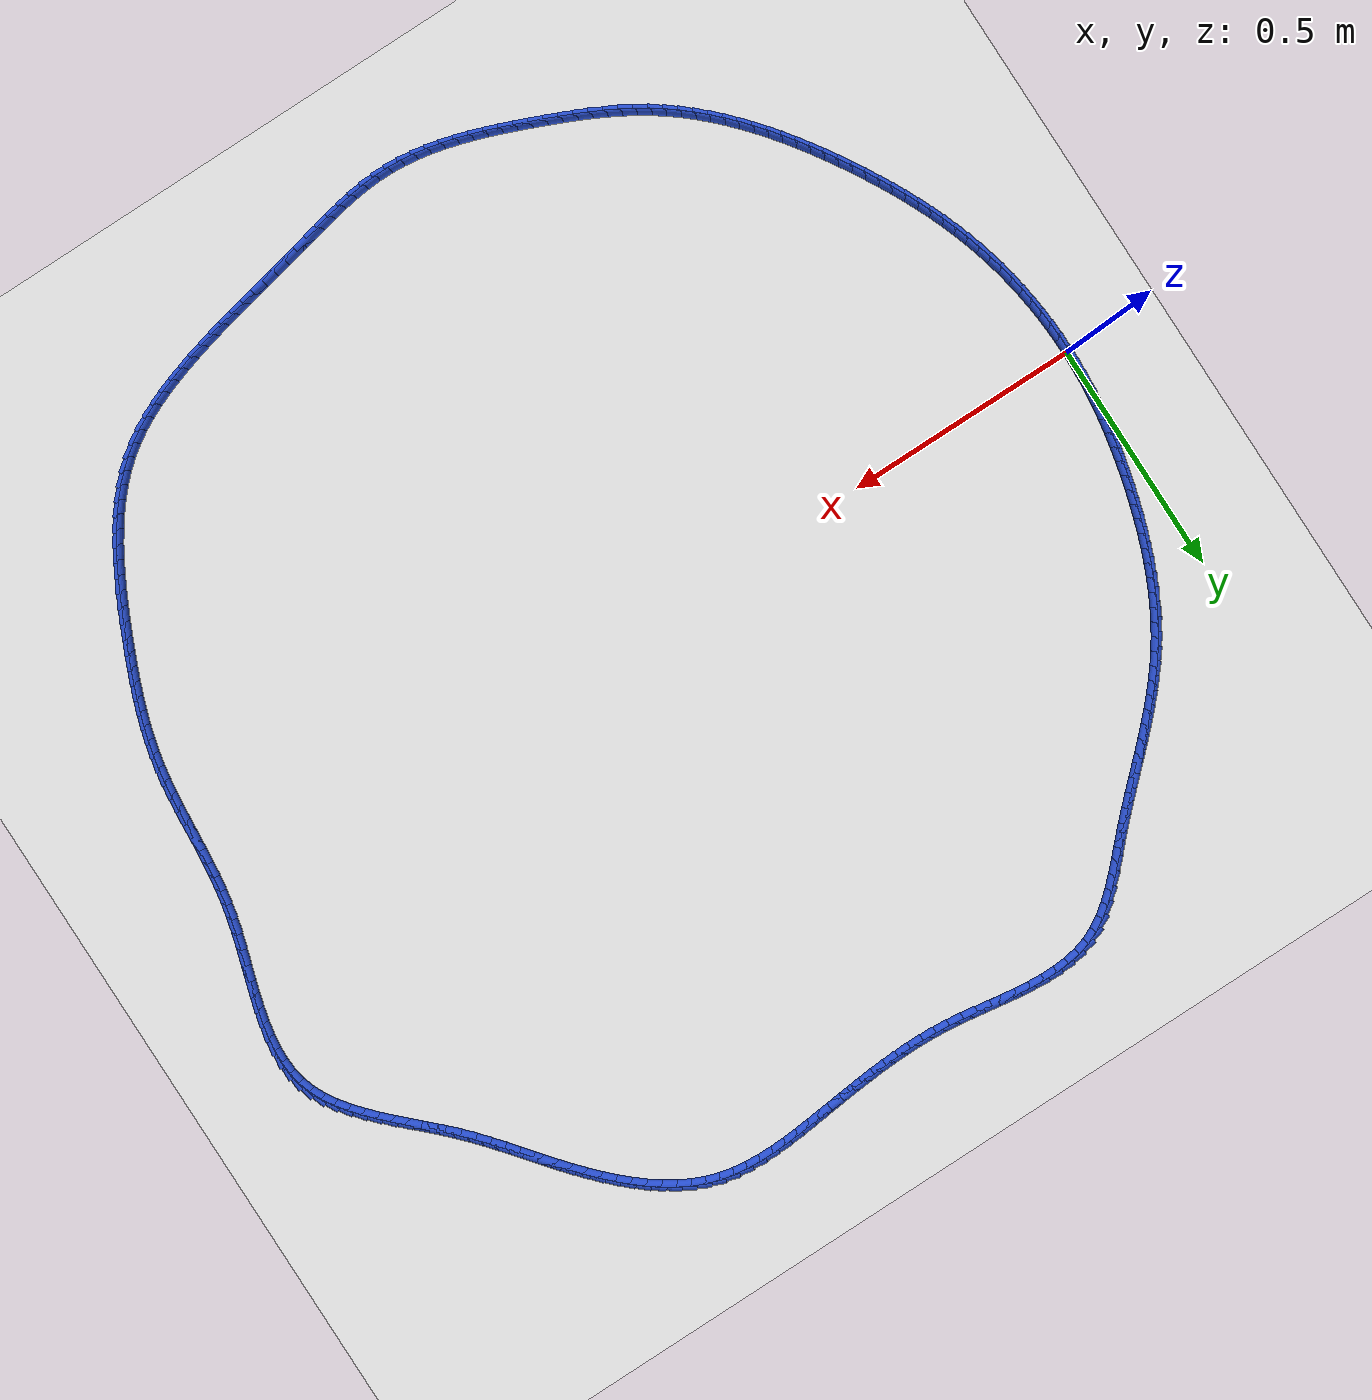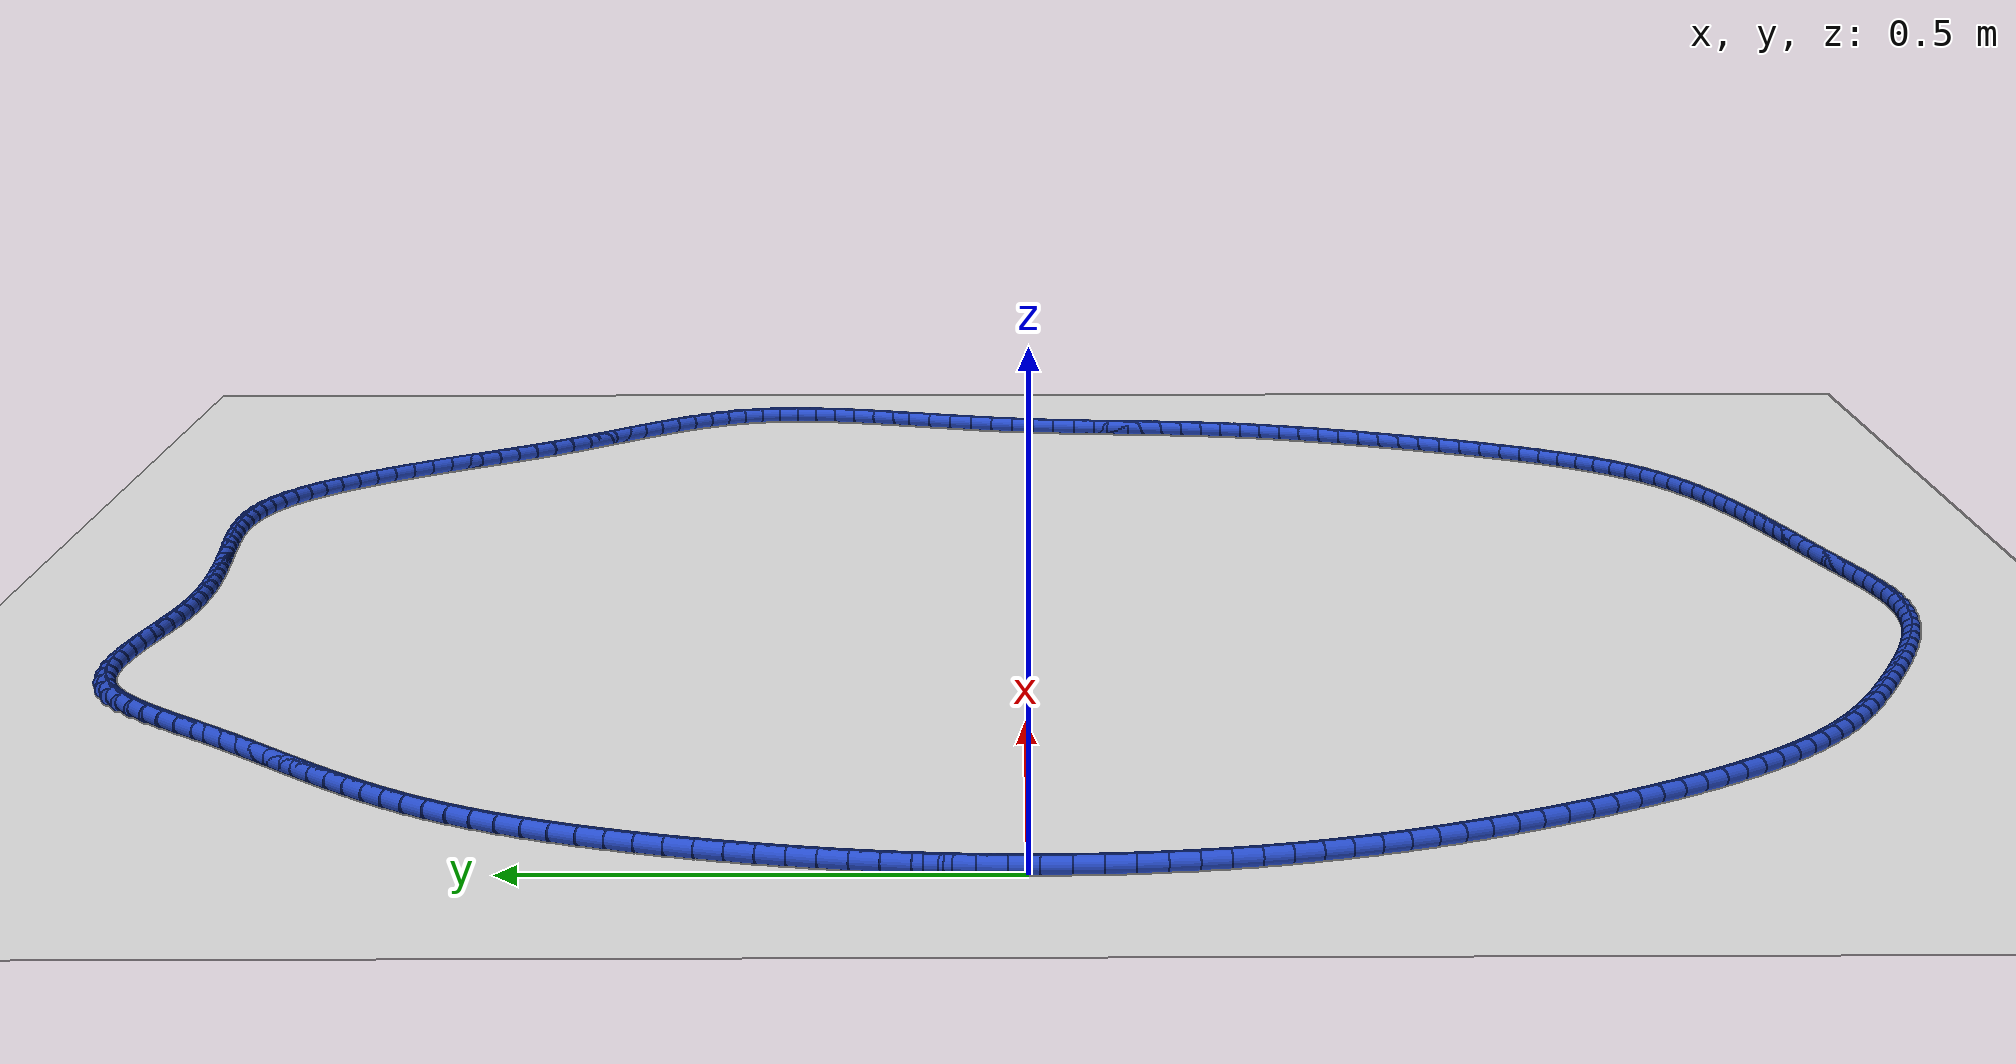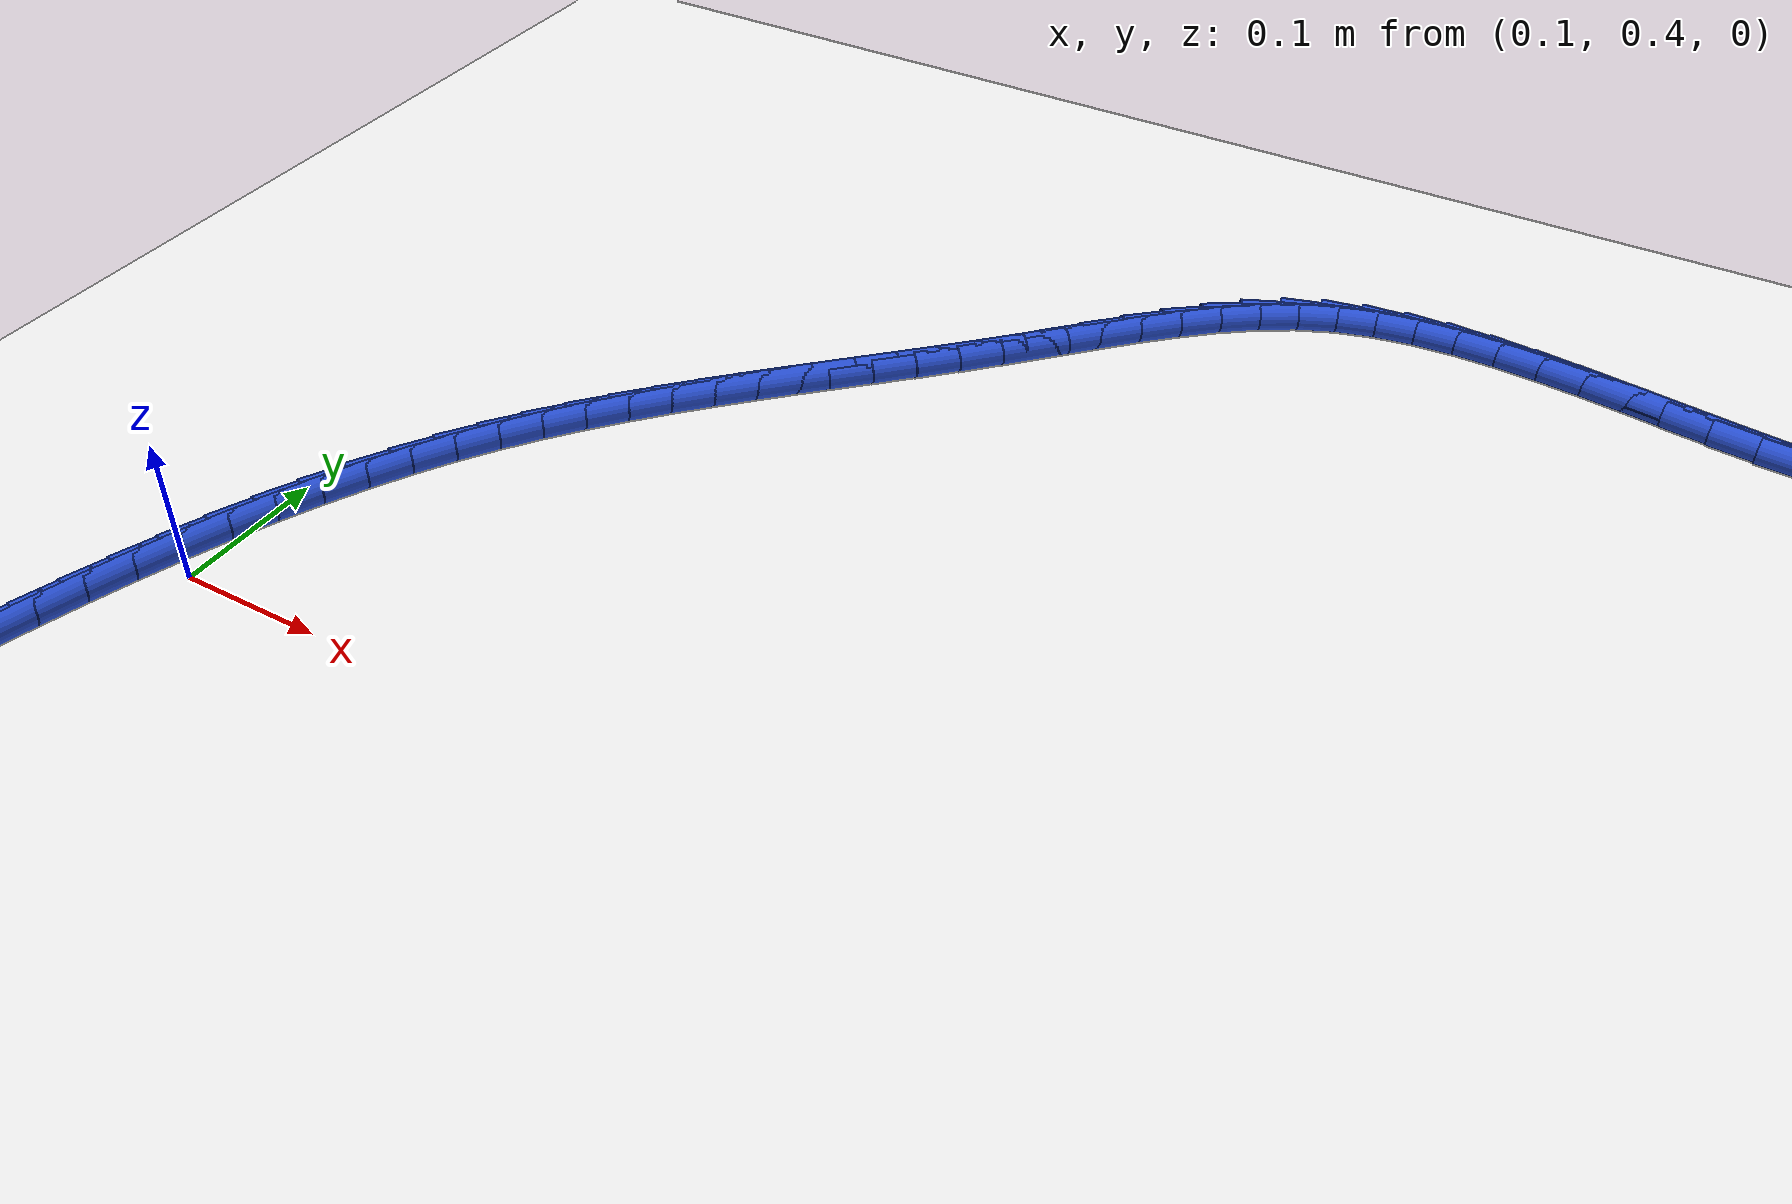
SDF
<sdf version="1.6">
 <world name="default">
  <light name="sun" type="directional">
   <pose>0 0 10 0 -0 0</pose>
   <diffuse>0.8 0.8 0.8 1</diffuse>
   <specular>0.2 0.2 0.2 1</specular>
   <attenuation>
    <range>1000</range>
    <constant>0.9</constant>
    <linear>0.01</linear>
    <quadratic>0.001</quadratic>
   </attenuation>
   <direction>-0.5 0.1 -0.9</direction>
  </light>
  <model name="ground_plane">
   <static>1</static>
   <link name="link">
    <collision name="collision">
     <geometry><plane><normal>0 0 1</normal><size>100 100</size></plane></geometry>
     <surface><friction><ode><mu>100</mu><mu2>50</mu2></ode></friction></surface>
    </collision>
    <visual name="visual">
     <cast_shadows>0</cast_shadows>
     <geometry><plane><normal>0 0 1</normal><size>100 100</size></plane></geometry>
     <material>
      <script><uri>file://media/materials/scripts/gazebo.material</uri><name>Gazebo/WhiteGlow</name></script>
     </material>
    </visual>
   </link>
  </model>
  <gravity>0 0 -9.8</gravity>
  <magnetic_field>6e-06 2.3e-05 -4.2e-05</magnetic_field>
  <atmosphere type="adiabatic"/>
  <physics name="default_physics" default="0" type="ode">
   <max_step_size>0.001</max_step_size>
   <real_time_factor>1</real_time_factor>
   <real_time_update_rate>1000</real_time_update_rate>
  </physics>
  <scene><ambient>0.4 0.4 0.4 1</ambient><background>0.7 0.7 0.7 1</background><shadows>1</shadows></scene>
  <spherical_coordinates>
   <surface_model>EARTH_WGS84</surface_model>
   <latitude_deg>0</latitude_deg>
   <longitude_deg>0</longitude_deg>
   <elevation>0</elevation>
   <heading_deg>0</heading_deg>
  </spherical_coordinates>
  <model name="line">
   <link name="link_0">
    <pose>-2.5153490401663703e-17 -2.7755575615628914e-17 0.01 0 1.57 1.5464626414685878</pose>
    <collision name="collision">
     <geometry><cylinder><radius>0.01</radius><length>0.08</length></cylinder></geometry>
    </collision>
    <visual name="visual">
     <material>
      <script><name>Gazebo/Blue</name><uri>file://media/materials/scripts/gazebo.material</uri></script>
     </material>
     <geometry><cylinder><radius>0.01</radius><length>0.08</length></cylinder></geometry>
    </visual>
   </link>
   <link name="link_1">
    <pose>0.0007270755552898855 0.029873487412748315 0.01 0 1.57 1.5155445078928647</pose>
    <collision name="collision">
     <geometry><cylinder><radius>0.01</radius><length>0.08</length></cylinder></geometry>
    </collision>
    <visual name="visual">
     <material>
      <script><name>Gazebo/Blue</name><uri>file://media/materials/scripts/gazebo.material</uri></script>
     </material>
     <geometry><cylinder><radius>0.01</radius><length>0.08</length></cylinder></geometry>
    </visual>
   </link>
   <link name="link_2">
    <pose>0.0023753390440270235 0.05967496593672548 0.01 0 1.57 1.48583429547019</pose>
    <collision name="collision">
     <geometry><cylinder><radius>0.01</radius><length>0.08</length></cylinder></geometry>
    </collision>
    <visual name="visual">
     <material>
      <script><name>Gazebo/Blue</name><uri>file://media/materials/scripts/gazebo.material</uri></script>
     </material>
     <geometry><cylinder><radius>0.01</radius><length>0.08</length></cylinder></geometry>
    </visual>
   </link>
   <link name="link_3">
    <pose>0.004907457332730425 0.08940615970832055 0.01 0 1.57 1.4573828797232249</pose>
    <collision name="collision">
     <geometry><cylinder><radius>0.01</radius><length>0.08</length></cylinder></geometry>
    </collision>
    <visual name="visual">
     <material>
      <script><name>Gazebo/Blue</name><uri>file://media/materials/scripts/gazebo.material</uri></script>
     </material>
     <geometry><cylinder><radius>0.01</radius><length>0.08</length></cylinder></geometry>
    </visual>
   </link>
   <link name="link_4">
    <pose>0.008286097287919137 0.11906879286392277 0.01 0 1.57 1.4302287537072027</pose>
    <collision name="collision">
     <geometry><cylinder><radius>0.01</radius><length>0.08</length></cylinder></geometry>
    </collision>
    <visual name="visual">
     <material>
      <script><name>Gazebo/Blue</name><uri>file://media/materials/scripts/gazebo.material</uri></script>
     </material>
     <geometry><cylinder><radius>0.01</radius><length>0.08</length></cylinder></geometry>
    </visual>
   </link>
   <link name="link_5">
    <pose>0.012473925776112204 0.1486645895399213 0.01 0 1.57 1.4043990815565572</pose>
    <collision name="collision">
     <geometry><cylinder><radius>0.01</radius><length>0.08</length></cylinder></geometry>
    </collision>
    <visual name="visual">
     <material>
      <script><name>Gazebo/Blue</name><uri>file://media/materials/scripts/gazebo.material</uri></script>
     </material>
     <geometry><cylinder><radius>0.01</radius><length>0.08</length></cylinder></geometry>
    </visual>
   </link>
   <link name="link_6">
    <pose>0.01743360966382864 0.178195273872705 0.01 0 1.57 1.3799109075156035</pose>
    <collision name="collision">
     <geometry><cylinder><radius>0.01</radius><length>0.08</length></cylinder></geometry>
    </collision>
    <visual name="visual">
     <material>
      <script><name>Gazebo/Blue</name><uri>file://media/materials/scripts/gazebo.material</uri></script>
     </material>
     <geometry><cylinder><radius>0.01</radius><length>0.08</length></cylinder></geometry>
    </visual>
   </link>
   <link name="link_7">
    <pose>0.023127815817587515 0.20766256999866325 0.01 0 1.57 1.3567724485234616</pose>
    <collision name="collision">
     <geometry><cylinder><radius>0.01</radius><length>0.08</length></cylinder></geometry>
    </collision>
    <visual name="visual">
     <material>
      <script><name>Gazebo/Blue</name><uri>file://media/materials/scripts/gazebo.material</uri></script>
     </material>
     <geometry><cylinder><radius>0.01</radius><length>0.08</length></cylinder></geometry>
    </visual>
   </link>
   <link name="link_8">
    <pose>0.029519211103907858 0.23706820205418527 0.01 0 1.57 1.3349844094778982</pose>
    <collision name="collision">
     <geometry><cylinder><radius>0.01</radius><length>0.08</length></cylinder></geometry>
    </collision>
    <visual name="visual">
     <material>
      <script><name>Gazebo/Blue</name><uri>file://media/materials/scripts/gazebo.material</uri></script>
     </material>
     <geometry><cylinder><radius>0.01</radius><length>0.08</length></cylinder></geometry>
    </visual>
   </link>
   <link name="link_9">
    <pose>0.03657046238930871 0.26641389417566 0.01 0 1.57 1.314487193543084</pose>
    <collision name="collision">
     <geometry><cylinder><radius>0.01</radius><length>0.08</length></cylinder></geometry>
    </collision>
    <visual name="visual">
     <material>
      <script><name>Gazebo/Blue</name><uri>file://media/materials/scripts/gazebo.material</uri></script>
     </material>
     <geometry><cylinder><radius>0.01</radius><length>0.08</length></cylinder></geometry>
    </visual>
   </link>
   <link name="link_10">
    <pose>0.044245577073488154 0.2957000271134144 0.01 0 1.57 1.2938691671459757</pose>
    <collision name="collision">
     <geometry><cylinder><radius>0.01</radius><length>0.08</length></cylinder></geometry>
    </collision>
    <visual name="visual">
     <material>
      <script><name>Gazebo/Blue</name><uri>file://media/materials/scripts/gazebo.material</uri></script>
     </material>
     <geometry><cylinder><radius>0.01</radius><length>0.08</length></cylinder></geometry>
    </visual>
   </link>
   <link name="link_11">
    <pose>0.05254296489867593 0.3248925060611907 0.01 0 1.57 1.2715785965053803</pose>
    <collision name="collision">
     <geometry><cylinder><radius>0.01</radius><length>0.08</length></cylinder></geometry>
    </collision>
    <visual name="visual">
     <material>
      <script><name>Gazebo/Blue</name><uri>file://media/materials/scripts/gazebo.material</uri></script>
     </material>
     <geometry><cylinder><radius>0.01</radius><length>0.08</length></cylinder></geometry>
    </visual>
   </link>
   <link name="link_12">
    <pose>0.0614975466002706 0.35392064751794183 0.01 0 1.57 1.2474417422383317</pose>
    <collision name="collision">
     <geometry><cylinder><radius>0.01</radius><length>0.08</length></cylinder></geometry>
    </collision>
    <visual name="visual">
     <material>
      <script><name>Gazebo/Blue</name><uri>file://media/materials/scripts/gazebo.material</uri></script>
     </material>
     <geometry><cylinder><radius>0.01</radius><length>0.08</length></cylinder></geometry>
    </visual>
   </link>
   <link name="link_13">
    <pose>0.07114600564489133 0.3827120015000069 0.01 0 1.57 1.2213468025566816</pose>
    <collision name="collision">
     <geometry><cylinder><radius>0.01</radius><length>0.08</length></cylinder></geometry>
    </collision>
    <visual name="visual">
     <material>
      <script><name>Gazebo/Blue</name><uri>file://media/materials/scripts/gazebo.material</uri></script>
     </material>
     <geometry><cylinder><radius>0.01</radius><length>0.08</length></cylinder></geometry>
    </visual>
   </link>
   <link name="link_14">
    <pose>0.08152502549915738 0.41119411802372496 0.01 0 1.57 1.1931741730922765</pose>
    <collision name="collision">
     <geometry><cylinder><radius>0.01</radius><length>0.08</length></cylinder></geometry>
    </collision>
    <visual name="visual">
     <material>
      <script><name>Gazebo/Blue</name><uri>file://media/materials/scripts/gazebo.material</uri></script>
     </material>
     <geometry><cylinder><radius>0.01</radius><length>0.08</length></cylinder></geometry>
    </visual>
   </link>
   <link name="link_15">
    <pose>0.092671289629688 0.4392945471054355 0.01 0 1.57 1.1627984171595789</pose>
    <collision name="collision">
     <geometry><cylinder><radius>0.01</radius><length>0.08</length></cylinder></geometry>
    </collision>
    <visual name="visual">
     <material>
      <script><name>Gazebo/Blue</name><uri>file://media/materials/scripts/gazebo.material</uri></script>
     </material>
     <geometry><cylinder><radius>0.01</radius><length>0.08</length></cylinder></geometry>
    </visual>
   </link>
   <link name="link_16">
    <pose>0.1046214815031024 0.4669408387614776 0.01 0 1.57 1.1300910325508897</pose>
    <collision name="collision">
     <geometry><cylinder><radius>0.01</radius><length>0.08</length></cylinder></geometry>
    </collision>
    <visual name="visual">
     <material>
      <script><name>Gazebo/Blue</name><uri>file://media/materials/scripts/gazebo.material</uri></script>
     </material>
     <geometry><cylinder><radius>0.01</radius><length>0.08</length></cylinder></geometry>
    </visual>
   </link>
   <link name="link_17">
    <pose>0.11741228458601984 0.49406054300819063 0.01 0 1.57 1.094924238850136</pose>
    <collision name="collision">
     <geometry><cylinder><radius>0.01</radius><length>0.08</length></cylinder></geometry>
    </collision>
    <visual name="visual">
     <material>
      <script><name>Gazebo/Blue</name><uri>file://media/materials/scripts/gazebo.material</uri></script>
     </material>
     <geometry><cylinder><radius>0.01</radius><length>0.08</length></cylinder></geometry>
    </visual>
   </link>
   <link name="link_18">
    <pose>0.13108038234505953 0.5205812098619137 0.01 0 1.57 1.0571760160030272</pose>
    <collision name="collision">
     <geometry><cylinder><radius>0.01</radius><length>0.08</length></cylinder></geometry>
    </collision>
    <visual name="visual">
     <material>
      <script><name>Gazebo/Blue</name><uri>file://media/materials/scripts/gazebo.material</uri></script>
     </material>
     <geometry><cylinder><radius>0.01</radius><length>0.08</length></cylinder></geometry>
    </visual>
   </link>
   <link name="link_19">
    <pose>0.1456624582468407 0.5464303893389861 0.01 0 1.57 1.0167366031096678</pose>
    <collision name="collision">
     <geometry><cylinder><radius>0.01</radius><length>0.08</length></cylinder></geometry>
    </collision>
    <visual name="visual">
     <material>
      <script><name>Gazebo/Blue</name><uri>file://media/materials/scripts/gazebo.material</uri></script>
     </material>
     <geometry><cylinder><radius>0.01</radius><length>0.08</length></cylinder></geometry>
    </visual>
   </link>
   <link name="link_20">
    <pose>0.16119519575798263 0.5715356314557472 0.01 0 1.57 0.973535501526441</pose>
    <collision name="collision">
     <geometry><cylinder><radius>0.01</radius><length>0.08</length></cylinder></geometry>
    </collision>
    <visual name="visual">
     <material>
      <script><name>Gazebo/Blue</name><uri>file://media/materials/scripts/gazebo.material</uri></script>
     </material>
     <geometry><cylinder><radius>0.01</radius><length>0.08</length></cylinder></geometry>
    </visual>
   </link>
   <link name="link_21">
    <pose>0.17771493513567257 0.5958249689958518 0.01 0 1.57 0.9298837224916326</pose>
    <collision name="collision">
     <geometry><cylinder><radius>0.01</radius><length>0.08</length></cylinder></geometry>
    </collision>
    <visual name="visual">
     <material>
      <script><name>Gazebo/Blue</name><uri>file://media/materials/scripts/gazebo.material</uri></script>
     </material>
     <geometry><cylinder><radius>0.01</radius><length>0.08</length></cylinder></geometry>
    </visual>
   </link>
   <link name="link_22">
    <pose>0.19521583272180534 0.6192857717356759 0.01 0 1.57 0.8905648073119198</pose>
    <collision name="collision">
     <geometry><cylinder><radius>0.01</radius><length>0.08</length></cylinder></geometry>
    </collision>
    <visual name="visual">
     <material>
      <script><name>Gazebo/Blue</name><uri>file://media/materials/scripts/gazebo.material</uri></script>
     </material>
     <geometry><cylinder><radius>0.01</radius><length>0.08</length></cylinder></geometry>
    </visual>
   </link>
   <link name="link_23">
    <pose>0.2136097624296306 0.642021150056412 0.01 0 1.57 0.8563678550724898</pose>
    <collision name="collision">
     <geometry><cylinder><radius>0.01</radius><length>0.08</length></cylinder></geometry>
    </collision>
    <visual name="visual">
     <material>
      <script><name>Gazebo/Blue</name><uri>file://media/materials/scripts/gazebo.material</uri></script>
     </material>
     <geometry><cylinder><radius>0.01</radius><length>0.08</length></cylinder></geometry>
    </visual>
   </link>
   <link name="link_24">
    <pose>0.2327990947141584 0.6641475821508581 0.01 0 1.57 0.8274449893817979</pose>
    <collision name="collision">
     <geometry><cylinder><radius>0.01</radius><length>0.08</length></cylinder></geometry>
    </collision>
    <visual name="visual">
     <material>
      <script><name>Gazebo/Blue</name><uri>file://media/materials/scripts/gazebo.material</uri></script>
     </material>
     <geometry><cylinder><radius>0.01</radius><length>0.08</length></cylinder></geometry>
    </visual>
   </link>
   <link name="link_25">
    <pose>0.25268620003039877 0.685781546211812 0.01 0 1.57 0.8038586675606355</pose>
    <collision name="collision">
     <geometry><cylinder><radius>0.01</radius><length>0.08</length></cylinder></geometry>
    </collision>
    <visual name="visual">
     <material>
      <script><name>Gazebo/Blue</name><uri>file://media/materials/scripts/gazebo.material</uri></script>
     </material>
     <geometry><cylinder><radius>0.01</radius><length>0.08</length></cylinder></geometry>
    </visual>
   </link>
   <link name="link_26">
    <pose>0.2731734488333616 0.7070395204320706 0.01 0 1.57 0.7856053602360004</pose>
    <collision name="collision">
     <geometry><cylinder><radius>0.01</radius><length>0.08</length></cylinder></geometry>
    </collision>
    <visual name="visual">
     <material>
      <script><name>Gazebo/Blue</name><uri>file://media/materials/scripts/gazebo.material</uri></script>
     </material>
     <geometry><cylinder><radius>0.01</radius><length>0.08</length></cylinder></geometry>
    </visual>
   </link>
   <link name="link_27">
    <pose>0.2941632115780569 0.7280379830044326 0.01 0 1.57 0.7726363225102736</pose>
    <collision name="collision">
     <geometry><cylinder><radius>0.01</radius><length>0.08</length></cylinder></geometry>
    </collision>
    <visual name="visual">
     <material>
      <script><name>Gazebo/Blue</name><uri>file://media/materials/scripts/gazebo.material</uri></script>
     </material>
     <geometry><cylinder><radius>0.01</radius><length>0.08</length></cylinder></geometry>
    </visual>
   </link>
   <link name="link_28">
    <pose>0.3155578587194946 0.748893412121695 0.01 0 1.57 0.7648740715352811</pose>
    <collision name="collision">
     <geometry><cylinder><radius>0.01</radius><length>0.08</length></cylinder></geometry>
    </collision>
    <visual name="visual">
     <material>
      <script><name>Gazebo/Blue</name><uri>file://media/materials/scripts/gazebo.material</uri></script>
     </material>
     <geometry><cylinder><radius>0.01</radius><length>0.08</length></cylinder></geometry>
    </visual>
   </link>
   <link name="link_29">
    <pose>0.33725976071268504 0.7697222859766563 0.01 0 1.57 0.7622240964671431</pose>
    <collision name="collision">
     <geometry><cylinder><radius>0.01</radius><length>0.08</length></cylinder></geometry>
    </collision>
    <visual name="visual">
     <material>
      <script><name>Gazebo/Blue</name><uri>file://media/materials/scripts/gazebo.material</uri></script>
     </material>
     <geometry><cylinder><radius>0.01</radius><length>0.08</length></cylinder></geometry>
    </visual>
   </link>
   <link name="link_30">
    <pose>0.35917128801263787 0.7906410827621134 0.01 0 1.57 0.7645818940894202</pose>
    <collision name="collision">
     <geometry><cylinder><radius>0.01</radius><length>0.08</length></cylinder></geometry>
    </collision>
    <visual name="visual">
     <material>
      <script><name>Gazebo/Blue</name><uri>file://media/materials/scripts/gazebo.material</uri></script>
     </material>
     <geometry><cylinder><radius>0.01</radius><length>0.08</length></cylinder></geometry>
    </visual>
   </link>
   <link name="link_31">
    <pose>0.38119481107436315 0.8117662806708648 0.01 0 1.57 0.7718357215952888</pose>
    <collision name="collision">
     <geometry><cylinder><radius>0.01</radius><length>0.08</length></cylinder></geometry>
    </collision>
    <visual name="visual">
     <material>
      <script><name>Gazebo/Blue</name><uri>file://media/materials/scripts/gazebo.material</uri></script>
     </material>
     <geometry><cylinder><radius>0.01</radius><length>0.08</length></cylinder></geometry>
    </visual>
   </link>
   <link name="link_32">
    <pose>0.4032327003528711 0.8332143578957077 0.01 0 1.57 0.783865590272139</pose>
    <collision name="collision">
     <geometry><cylinder><radius>0.01</radius><length>0.08</length></cylinder></geometry>
    </collision>
    <visual name="visual">
     <material>
      <script><name>Gazebo/Blue</name><uri>file://media/materials/scripts/gazebo.material</uri></script>
     </material>
     <geometry><cylinder><radius>0.01</radius><length>0.08</length></cylinder></geometry>
    </visual>
   </link>
   <link name="link_33">
    <pose>0.42518732630317146 0.8551017926294397 0.01 0 1.57 0.7995488786064916</pose>
    <collision name="collision">
     <geometry><cylinder><radius>0.01</radius><length>0.08</length></cylinder></geometry>
    </collision>
    <visual name="visual">
     <material>
      <script><name>Gazebo/Blue</name><uri>file://media/materials/scripts/gazebo.material</uri></script>
     </material>
     <geometry><cylinder><radius>0.01</radius><length>0.08</length></cylinder></geometry>
    </visual>
   </link>
   <link name="link_34">
    <pose>0.44697429958128687 0.8775142613748956 0.01 0 1.57 0.8061112273929352</pose>
    <collision name="collision">
     <geometry><cylinder><radius>0.01</radius><length>0.08</length></cylinder></geometry>
    </collision>
    <visual name="visual">
     <material>
      <script><name>Gazebo/Blue</name><uri>file://media/materials/scripts/gazebo.material</uri></script>
     </material>
     <geometry><cylinder><radius>0.01</radius><length>0.08</length></cylinder></geometry>
    </visual>
   </link>
   <link name="link_35">
    <pose>0.4686805549670649 0.9001388762520655 0.01 0 1.57 0.794795504380084</pose>
    <collision name="collision">
     <geometry><cylinder><radius>0.01</radius><length>0.08</length></cylinder></geometry>
    </collision>
    <visual name="visual">
     <material>
      <script><name>Gazebo/Blue</name><uri>file://media/materials/scripts/gazebo.material</uri></script>
     </material>
     <geometry><cylinder><radius>0.01</radius><length>0.08</length></cylinder></geometry>
    </visual>
   </link>
   <link name="link_36">
    <pose>0.49051242831453784 0.9223849775506759 0.01 0 1.57 0.7647972383553288</pose>
    <collision name="collision">
     <geometry><cylinder><radius>0.01</radius><length>0.08</length></cylinder></geometry>
    </collision>
    <visual name="visual">
     <material>
      <script><name>Gazebo/Blue</name><uri>file://media/materials/scripts/gazebo.material</uri></script>
     </material>
     <geometry><cylinder><radius>0.01</radius><length>0.08</length></cylinder></geometry>
    </visual>
   </link>
   <link name="link_37">
    <pose>0.5126786847941239 0.9436562540563649 0.01 0 1.57 0.7145596531466036</pose>
    <collision name="collision">
     <geometry><cylinder><radius>0.01</radius><length>0.08</length></cylinder></geometry>
    </collision>
    <visual name="visual">
     <material>
      <script><name>Gazebo/Blue</name><uri>file://media/materials/scripts/gazebo.material</uri></script>
     </material>
     <geometry><cylinder><radius>0.01</radius><length>0.08</length></cylinder></geometry>
    </visual>
   </link>
   <link name="link_38">
    <pose>0.5353880895762421 0.9633563945547692 0.01 0 1.57 0.6417722395684741</pose>
    <collision name="collision">
     <geometry><cylinder><radius>0.01</radius><length>0.08</length></cylinder></geometry>
    </collision>
    <visual name="visual">
     <material>
      <script><name>Gazebo/Blue</name><uri>file://media/materials/scripts/gazebo.material</uri></script>
     </material>
     <geometry><cylinder><radius>0.01</radius><length>0.08</length></cylinder></geometry>
    </visual>
   </link>
   <link name="link_39">
    <pose>0.5588494078313107 0.9808890878315272 0.01 0 1.57 0.5438968007247597</pose>
    <collision name="collision">
     <geometry><cylinder><radius>0.01</radius><length>0.08</length></cylinder></geometry>
    </collision>
    <visual name="visual">
     <material>
      <script><name>Gazebo/Blue</name><uri>file://media/materials/scripts/gazebo.material</uri></script>
     </material>
     <geometry><cylinder><radius>0.01</radius><length>0.08</length></cylinder></geometry>
    </visual>
   </link>
   <link name="link_40">
    <pose>0.5832714047297484 0.995658022672276 0.01 0 1.57 0.41961008747286194</pose>
    <collision name="collision">
     <geometry><cylinder><radius>0.01</radius><length>0.08</length></cylinder></geometry>
    </collision>
    <visual name="visual">
     <material>
      <script><name>Gazebo/Blue</name><uri>file://media/materials/scripts/gazebo.material</uri></script>
     </material>
     <geometry><cylinder><radius>0.01</radius><length>0.08</length></cylinder></geometry>
    </visual>
   </link>
   <link name="link_41">
    <pose>0.6088605576240415 1.0070734705995863 0.01 0 1.57 0.2850498647237634</pose>
    <collision name="collision">
     <geometry><cylinder><radius>0.01</radius><length>0.08</length></cylinder></geometry>
    </collision>
    <visual name="visual">
     <material>
      <script><name>Gazebo/Blue</name><uri>file://media/materials/scripts/gazebo.material</uri></script>
     </material>
     <geometry><cylinder><radius>0.01</radius><length>0.08</length></cylinder></geometry>
    </visual>
   </link>
   <link name="link_42">
    <pose>0.6356881320541202 1.0149347479895159 0.01 0 1.57 0.16693370517301895</pose>
    <collision name="collision">
     <geometry><cylinder><radius>0.01</radius><length>0.08</length></cylinder></geometry>
    </collision>
    <visual name="visual">
     <material>
      <script><name>Gazebo/Blue</name><uri>file://media/materials/scripts/gazebo.material</uri></script>
     </material>
     <geometry><cylinder><radius>0.01</radius><length>0.08</length></cylinder></geometry>
    </visual>
   </link>
   <link name="link_43">
    <pose>0.6636169896949902 1.0196408115125841 0.01 0 1.57 0.06918742205419548</pose>
    <collision name="collision">
     <geometry><cylinder><radius>0.01</radius><length>0.08</length></cylinder></geometry>
    </collision>
    <visual name="visual">
     <material>
      <script><name>Gazebo/Blue</name><uri>file://media/materials/scripts/gazebo.material</uri></script>
     </material>
     <geometry><cylinder><radius>0.01</radius><length>0.08</length></cylinder></geometry>
    </visual>
   </link>
   <link name="link_44">
    <pose>0.692492201573911 1.0216418068575974 0.01 0 1.57 -0.008559141441000867</pose>
    <collision name="collision">
     <geometry><cylinder><radius>0.01</radius><length>0.08</length></cylinder></geometry>
    </collision>
    <visual name="visual">
     <material>
      <script><name>Gazebo/Blue</name><uri>file://media/materials/scripts/gazebo.material</uri></script>
     </material>
     <geometry><cylinder><radius>0.01</radius><length>0.08</length></cylinder></geometry>
    </visual>
   </link>
   <link name="link_45">
    <pose>0.7221588387181427 1.0213878797133629 0.01 0 1.57 -0.06783276782823092</pose>
    <collision name="collision">
     <geometry><cylinder><radius>0.01</radius><length>0.08</length></cylinder></geometry>
    </collision>
    <visual name="visual">
     <material>
      <script><name>Gazebo/Blue</name><uri>file://media/materials/scripts/gazebo.material</uri></script>
     </material>
     <geometry><cylinder><radius>0.01</radius><length>0.08</length></cylinder></geometry>
    </visual>
   </link>
   <link name="link_46">
    <pose>0.752461972154945 1.019329175768687 0.01 0 1.57 -0.1104265941994296</pose>
    <collision name="collision">
     <geometry><cylinder><radius>0.01</radius><length>0.08</length></cylinder></geometry>
    </collision>
    <visual name="visual">
     <material>
      <script><name>Gazebo/Blue</name><uri>file://media/materials/scripts/gazebo.material</uri></script>
     </material>
     <geometry><cylinder><radius>0.01</radius><length>0.08</length></cylinder></geometry>
    </visual>
   </link>
   <link name="link_47">
    <pose>0.7832466729115781 1.015915840712377 0.01 0 1.57 -0.13790514897232956</pose>
    <collision name="collision">
     <geometry><cylinder><radius>0.01</radius><length>0.08</length></cylinder></geometry>
    </collision>
    <visual name="visual">
     <material>
      <script><name>Gazebo/Blue</name><uri>file://media/materials/scripts/gazebo.material</uri></script>
     </material>
     <geometry><cylinder><radius>0.01</radius><length>0.08</length></cylinder></geometry>
    </visual>
   </link>
   <link name="link_48">
    <pose>0.8143580120153019 1.0115980202332393 0.01 0 1.57 -0.15138074713984573</pose>
    <collision name="collision">
     <geometry><cylinder><radius>0.01</radius><length>0.08</length></cylinder></geometry>
    </collision>
    <visual name="visual">
     <material>
      <script><name>Gazebo/Blue</name><uri>file://media/materials/scripts/gazebo.material</uri></script>
     </material>
     <geometry><cylinder><radius>0.01</radius><length>0.08</length></cylinder></geometry>
    </visual>
   </link>
   <link name="link_49">
    <pose>0.8456410604933758 1.0068258600200806 0.01 0 1.57 -0.15143177151995213</pose>
    <collision name="collision">
     <geometry><cylinder><radius>0.01</radius><length>0.08</length></cylinder></geometry>
    </collision>
    <visual name="visual">
     <material>
      <script><name>Gazebo/Blue</name><uri>file://media/materials/scripts/gazebo.material</uri></script>
     </material>
     <geometry><cylinder><radius>0.01</radius><length>0.08</length></cylinder></geometry>
    </visual>
   </link>
   <link name="link_50">
    <pose>0.8769408893730603 1.0020495057617078 0.01 0 1.57 -0.13808131413352706</pose>
    <collision name="collision">
     <geometry><cylinder><radius>0.01</radius><length>0.08</length></cylinder></geometry>
    </collision>
    <visual name="visual">
     <material>
      <script><name>Gazebo/Blue</name><uri>file://media/materials/scripts/gazebo.material</uri></script>
     </material>
     <geometry><cylinder><radius>0.01</radius><length>0.08</length></cylinder></geometry>
    </visual>
   </link>
   <link name="link_51">
    <pose>0.9081025696816147 0.9977191031469279 0.01 0 1.57 -0.11081628932290162</pose>
    <collision name="collision">
     <geometry><cylinder><radius>0.01</radius><length>0.08</length></cylinder></geometry>
    </collision>
    <visual name="visual">
     <material>
      <script><name>Gazebo/Blue</name><uri>file://media/materials/scripts/gazebo.material</uri></script>
     </material>
     <geometry><cylinder><radius>0.01</radius><length>0.08</length></cylinder></geometry>
    </visual>
   </link>
   <link name="link_52">
    <pose>0.9389713829575411 0.9942842640519602 0.01 0 1.57 -0.07350329960058424</pose>
    <collision name="collision">
     <geometry><cylinder><radius>0.01</radius><length>0.08</length></cylinder></geometry>
    </collision>
    <visual name="visual">
     <material>
      <script><name>Gazebo/Blue</name><uri>file://media/materials/scripts/gazebo.material</uri></script>
     </material>
     <geometry><cylinder><radius>0.01</radius><length>0.08</length></cylinder></geometry>
    </visual>
   </link>
   <link name="link_53">
    <pose>0.9694537086662779 0.9920396687582569 0.01 0 1.57 -0.037415986823284494</pose>
    <collision name="collision">
     <geometry><cylinder><radius>0.01</radius><length>0.08</length></cylinder></geometry>
    </collision>
    <visual name="visual">
     <material>
      <script><name>Gazebo/Blue</name><uri>file://media/materials/scripts/gazebo.material</uri></script>
     </material>
     <geometry><cylinder><radius>0.01</radius><length>0.08</length></cylinder></geometry>
    </visual>
   </link>
   <link name="link_54">
    <pose>0.9996013880215336 0.9909111369039175 0.01 0 1.57 -0.004696522407320155</pose>
    <collision name="collision">
     <geometry><cylinder><radius>0.01</radius><length>0.08</length></cylinder></geometry>
    </collision>
    <visual name="visual">
     <material>
      <script><name>Gazebo/Blue</name><uri>file://media/materials/scripts/gazebo.material</uri></script>
     </material>
     <geometry><cylinder><radius>0.01</radius><length>0.08</length></cylinder></geometry>
    </visual>
   </link>
   <link name="link_55">
    <pose>1.0294874441008635 0.9907707753398729 0.01 0 1.57 0.024236911349796126</pose>
    <collision name="collision">
     <geometry><cylinder><radius>0.01</radius><length>0.08</length></cylinder></geometry>
    </collision>
    <visual name="visual">
     <material>
      <script><name>Gazebo/Blue</name><uri>file://media/materials/scripts/gazebo.material</uri></script>
     </material>
     <geometry><cylinder><radius>0.01</radius><length>0.08</length></cylinder></geometry>
    </visual>
   </link>
   <link name="link_56">
    <pose>1.0591848999818223 0.9914906909170534 0.01 0 1.57 0.049054844252991975</pose>
    <collision name="collision">
     <geometry><cylinder><radius>0.01</radius><length>0.08</length></cylinder></geometry>
    </collision>
    <visual name="visual">
     <material>
      <script><name>Gazebo/Blue</name><uri>file://media/materials/scripts/gazebo.material</uri></script>
     </material>
     <geometry><cylinder><radius>0.01</radius><length>0.08</length></cylinder></geometry>
    </visual>
   </link>
   <link name="link_57">
    <pose>1.0887667787419666 0.9929429904863905 0.01 0 1.57 0.06951669238525317</pose>
    <collision name="collision">
     <geometry><cylinder><radius>0.01</radius><length>0.08</length></cylinder></geometry>
    </collision>
    <visual name="visual">
     <material>
      <script><name>Gazebo/Blue</name><uri>file://media/materials/scripts/gazebo.material</uri></script>
     </material>
     <geometry><cylinder><radius>0.01</radius><length>0.08</length></cylinder></geometry>
    </visual>
   </link>
   <link name="link_58">
    <pose>1.118306103458851 0.9949997808988147 0.01 0 1.57 0.08546616097080703</pose>
    <collision name="collision">
     <geometry><cylinder><radius>0.01</radius><length>0.08</length></cylinder></geometry>
    </collision>
    <visual name="visual">
     <material>
      <script><name>Gazebo/Blue</name><uri>file://media/materials/scripts/gazebo.material</uri></script>
     </material>
     <geometry><cylinder><radius>0.01</radius><length>0.08</length></cylinder></geometry>
    </visual>
   </link>
   <link name="link_59">
    <pose>1.1478758972100318 0.997533169005257 0.01 0 1.57 0.09682381098356786</pose>
    <collision name="collision">
     <geometry><cylinder><radius>0.01</radius><length>0.08</length></cylinder></geometry>
    </collision>
    <visual name="visual">
     <material>
      <script><name>Gazebo/Blue</name><uri>file://media/materials/scripts/gazebo.material</uri></script>
     </material>
     <geometry><cylinder><radius>0.01</radius><length>0.08</length></cylinder></geometry>
    </visual>
   </link>
   <link name="link_60">
    <pose>1.177549183073063 1.0004152616566482 0.01 0 1.57 0.10357856573783551</pose>
    <collision name="collision">
     <geometry><cylinder><radius>0.01</radius><length>0.08</length></cylinder></geometry>
    </collision>
    <visual name="visual">
     <material>
      <script><name>Gazebo/Blue</name><uri>file://media/materials/scripts/gazebo.material</uri></script>
     </material>
     <geometry><cylinder><radius>0.01</radius><length>0.08</length></cylinder></geometry>
    </visual>
   </link>
   <link name="link_61">
    <pose>1.207398984125502 1.0035181657039196 0.01 0 1.57 0.10577950151761183</pose>
    <collision name="collision">
     <geometry><cylinder><radius>0.01</radius><length>0.08</length></cylinder></geometry>
    </collision>
    <visual name="visual">
     <material>
      <script><name>Gazebo/Blue</name><uri>file://media/materials/scripts/gazebo.material</uri></script>
     </material>
     <geometry><cylinder><radius>0.01</radius><length>0.08</length></cylinder></geometry>
    </visual>
   </link>
   <link name="link_62">
    <pose>1.2374983227003518 1.006713987307407 0.01 0 1.57 0.10248181696850574</pose>
    <collision name="collision">
     <geometry><cylinder><radius>0.01</radius><length>0.08</length></cylinder></geometry>
    </collision>
    <visual name="visual">
     <material>
      <script><name>Gazebo/Blue</name><uri>file://media/materials/scripts/gazebo.material</uri></script>
     </material>
     <geometry><cylinder><radius>0.01</radius><length>0.08</length></cylinder></geometry>
    </visual>
   </link>
   <link name="link_63">
    <pose>1.267881184285906 1.0098386246925761 0.01 0 1.57 0.08994871352086782</pose>
    <collision name="collision">
     <geometry><cylinder><radius>0.01</radius><length>0.08</length></cylinder></geometry>
    </collision>
    <visual name="visual">
     <material>
      <script><name>Gazebo/Blue</name><uri>file://media/materials/scripts/gazebo.material</uri></script>
     </material>
     <geometry><cylinder><radius>0.01</radius><length>0.08</length></cylinder></geometry>
    </visual>
   </link>
   <link name="link_64">
    <pose>1.298437740697516 1.012594584256188 0.01 0 1.57 0.06721661303895507</pose>
    <collision name="collision">
     <geometry><cylinder><radius>0.01</radius><length>0.08</length></cylinder></geometry>
    </collision>
    <visual name="visual">
     <material>
      <script><name>Gazebo/Blue</name><uri>file://media/materials/scripts/gazebo.material</uri></script>
     </material>
     <geometry><cylinder><radius>0.01</radius><length>0.08</length></cylinder></geometry>
    </visual>
   </link>
   <link name="link_65">
    <pose>1.3290250537468487 1.0146536617966984 0.01 0 1.57 0.03391600854188288</pose>
    <collision name="collision">
     <geometry><cylinder><radius>0.01</radius><length>0.08</length></cylinder></geometry>
    </collision>
    <visual name="visual">
     <material>
      <script><name>Gazebo/Blue</name><uri>file://media/materials/scripts/gazebo.material</uri></script>
     </material>
     <geometry><cylinder><radius>0.01</radius><length>0.08</length></cylinder></geometry>
    </visual>
   </link>
   <link name="link_66">
    <pose>1.35950018524557 1.0156876531125634 0.01 0 1.57 -0.010565423728079532</pose>
    <collision name="collision">
     <geometry><cylinder><radius>0.01</radius><length>0.08</length></cylinder></geometry>
    </collision>
    <visual name="visual">
     <material>
      <script><name>Gazebo/Blue</name><uri>file://media/materials/scripts/gazebo.material</uri></script>
     </material>
     <geometry><cylinder><radius>0.01</radius><length>0.08</length></cylinder></geometry>
    </visual>
   </link>
   <link name="link_67">
    <pose>1.3897201970053452 1.0153683540022393 0.01 0 1.57 -0.06699090916173436</pose>
    <collision name="collision">
     <geometry><cylinder><radius>0.01</radius><length>0.08</length></cylinder></geometry>
    </collision>
    <visual name="visual">
     <material>
      <script><name>Gazebo/Blue</name><uri>file://media/materials/scripts/gazebo.material</uri></script>
     </material>
     <geometry><cylinder><radius>0.01</radius><length>0.08</length></cylinder></geometry>
    </visual>
   </link>
   <link name="link_68">
    <pose>1.4195421508378416 1.0133675602641823 0.01 0 1.57 -0.13611892987582064</pose>
    <collision name="collision">
     <geometry><cylinder><radius>0.01</radius><length>0.08</length></cylinder></geometry>
    </collision>
    <visual name="visual">
     <material>
      <script><name>Gazebo/Blue</name><uri>file://media/materials/scripts/gazebo.material</uri></script>
     </material>
     <geometry><cylinder><radius>0.01</radius><length>0.08</length></cylinder></geometry>
    </visual>
   </link>
   <link name="link_69">
    <pose>1.4488231085547247 1.0093570676968484 0.01 0 1.57 -0.2184523855704861</pose>
    <collision name="collision">
     <geometry><cylinder><radius>0.01</radius><length>0.08</length></cylinder></geometry>
    </collision>
    <visual name="visual">
     <material>
      <script><name>Gazebo/Blue</name><uri>file://media/materials/scripts/gazebo.material</uri></script>
     </material>
     <geometry><cylinder><radius>0.01</radius><length>0.08</length></cylinder></geometry>
    </visual>
   </link>
   <link name="link_70">
    <pose>1.4774201319676603 1.0030086720986942 0.01 0 1.57 -0.3134145112203563</pose>
    <collision name="collision">
     <geometry><cylinder><radius>0.01</radius><length>0.08</length></cylinder></geometry>
    </collision>
    <visual name="visual">
     <material>
      <script><name>Gazebo/Blue</name><uri>file://media/materials/scripts/gazebo.material</uri></script>
     </material>
     <geometry><cylinder><radius>0.01</radius><length>0.08</length></cylinder></geometry>
    </visual>
   </link>
   <link name="link_71">
    <pose>1.5051936838464097 0.9940073607158068 0.01 0 1.57 -0.4096489545835001</pose>
    <collision name="collision">
     <geometry><cylinder><radius>0.01</radius><length>0.08</length></cylinder></geometry>
    </collision>
    <visual name="visual">
     <material>
      <script><name>Gazebo/Blue</name><uri>file://media/materials/scripts/gazebo.material</uri></script>
     </material>
     <geometry><cylinder><radius>0.01</radius><length>0.08</length></cylinder></geometry>
    </visual>
   </link>
   <link name="link_72">
    <pose>1.532080214059043 0.9823328553367062 0.01 0 1.57 -0.49609090253793314</pose>
    <collision name="collision">
     <geometry><cylinder><radius>0.01</radius><length>0.08</length></cylinder></geometry>
    </collision>
    <visual name="visual">
     <material>
      <script><name>Gazebo/Blue</name><uri>file://media/materials/scripts/gazebo.material</uri></script>
     </material>
     <geometry><cylinder><radius>0.01</radius><length>0.08</length></cylinder></geometry>
    </visual>
   </link>
   <link name="link_73">
    <pose>1.5580909382963097 0.9682548752761739 0.01 0 1.57 -0.5722398250840559</pose>
    <collision name="collision">
     <geometry><cylinder><radius>0.01</radius><length>0.08</length></cylinder></geometry>
    </collision>
    <visual name="visual">
     <material>
      <script><name>Gazebo/Blue</name><uri>file://media/materials/scripts/gazebo.material</uri></script>
     </material>
     <geometry><cylinder><radius>0.01</radius><length>0.08</length></cylinder></geometry>
    </visual>
   </link>
   <link name="link_74">
    <pose>1.5832402289318273 0.9520553838154171 0.01 0 1.57 -0.6385414616156481</pose>
    <collision name="collision">
     <geometry><cylinder><radius>0.01</radius><length>0.08</length></cylinder></geometry>
    </collision>
    <visual name="visual">
     <material>
      <script><name>Gazebo/Blue</name><uri>file://media/materials/scripts/gazebo.material</uri></script>
     </material>
     <geometry><cylinder><radius>0.01</radius><length>0.08</length></cylinder></geometry>
    </visual>
   </link>
   <link name="link_75">
    <pose>1.6075424583392115 0.9340163442356438 0.01 0 1.57 -0.6957099818627236</pose>
    <collision name="collision">
     <geometry><cylinder><radius>0.01</radius><length>0.08</length></cylinder></geometry>
    </collision>
    <visual name="visual">
     <material>
      <script><name>Gazebo/Blue</name><uri>file://media/materials/scripts/gazebo.material</uri></script>
     </material>
     <geometry><cylinder><radius>0.01</radius><length>0.08</length></cylinder></geometry>
    </visual>
   </link>
   <link name="link_76">
    <pose>1.6310119988920813 0.9144197198180616 0.01 0 1.57 -0.744546908092899</pose>
    <collision name="collision">
     <geometry><cylinder><radius>0.01</radius><length>0.08</length></cylinder></geometry>
    </collision>
    <visual name="visual">
     <material>
      <script><name>Gazebo/Blue</name><uri>file://media/materials/scripts/gazebo.material</uri></script>
     </material>
     <geometry><cylinder><radius>0.01</radius><length>0.08</length></cylinder></geometry>
    </visual>
   </link>
   <link name="link_77">
    <pose>1.6536632229640522 0.8935474738438784 0.01 0 1.57 -0.7858242198400484</pose>
    <collision name="collision">
     <geometry><cylinder><radius>0.01</radius><length>0.08</length></cylinder></geometry>
    </collision>
    <visual name="visual">
     <material>
      <script><name>Gazebo/Blue</name><uri>file://media/materials/scripts/gazebo.material</uri></script>
     </material>
     <geometry><cylinder><radius>0.01</radius><length>0.08</length></cylinder></geometry>
    </visual>
   </link>
   <link name="link_78">
    <pose>1.6755105029287416 0.8716815695943011 0.01 0 1.57 -0.8202157659437417</pose>
    <collision name="collision">
     <geometry><cylinder><radius>0.01</radius><length>0.08</length></cylinder></geometry>
    </collision>
    <visual name="visual">
     <material>
      <script><name>Gazebo/Blue</name><uri>file://media/materials/scripts/gazebo.material</uri></script>
     </material>
     <geometry><cylinder><radius>0.01</radius><length>0.08</length></cylinder></geometry>
    </visual>
   </link>
   <link name="link_79">
    <pose>1.6965682111597675 0.8491039703505384 0.01 0 1.57 -0.8482589207673639</pose>
    <collision name="collision">
     <geometry><cylinder><radius>0.01</radius><length>0.08</length></cylinder></geometry>
    </collision>
    <visual name="visual">
     <material>
      <script><name>Gazebo/Blue</name><uri>file://media/materials/scripts/gazebo.material</uri></script>
     </material>
     <geometry><cylinder><radius>0.01</radius><length>0.08</length></cylinder></geometry>
    </visual>
   </link>
   <link name="link_80">
    <pose>1.7168507200307466 0.8260966393937976 0.01 0 1.57 -0.8703094331605452</pose>
    <collision name="collision">
     <geometry><cylinder><radius>0.01</radius><length>0.08</length></cylinder></geometry>
    </collision>
    <visual name="visual">
     <material>
      <script><name>Gazebo/Blue</name><uri>file://media/materials/scripts/gazebo.material</uri></script>
     </material>
     <geometry><cylinder><radius>0.01</radius><length>0.08</length></cylinder></geometry>
    </visual>
   </link>
   <link name="link_81">
    <pose>1.7363789409900152 0.8029348156674097 0.01 0 1.57 -0.8860357209856227</pose>
    <collision name="collision">
     <geometry><cylinder><radius>0.01</radius><length>0.08</length></cylinder></geometry>
    </collision>
    <visual name="visual">
     <material>
      <script><name>Gazebo/Blue</name><uri>file://media/materials/scripts/gazebo.material</uri></script>
     </material>
     <geometry><cylinder><radius>0.01</radius><length>0.08</length></cylinder></geometry>
    </visual>
   </link>
   <link name="link_82">
    <pose>1.7552967210931634 0.7797673195316748 0.01 0 1.57 -0.894710031149734</pose>
    <collision name="collision">
     <geometry><cylinder><radius>0.01</radius><length>0.08</length></cylinder></geometry>
    </collision>
    <visual name="visual">
     <material>
      <script><name>Gazebo/Blue</name><uri>file://media/materials/scripts/gazebo.material</uri></script>
     </material>
     <geometry><cylinder><radius>0.01</radius><length>0.08</length></cylinder></geometry>
    </visual>
   </link>
   <link name="link_83">
    <pose>1.7738572819088314 0.7566304980670335 0.01 0 1.57 -0.8960183913171533</pose>
    <collision name="collision">
     <geometry><cylinder><radius>0.01</radius><length>0.08</length></cylinder></geometry>
    </collision>
    <visual name="visual">
     <material>
      <script><name>Gazebo/Blue</name><uri>file://media/materials/scripts/gazebo.material</uri></script>
     </material>
     <geometry><cylinder><radius>0.01</radius><length>0.08</length></cylinder></geometry>
    </visual>
   </link>
   <link name="link_84">
    <pose>1.7923176602408384 0.7335567750266206 0.01 0 1.57 -0.8898590115530806</pose>
    <collision name="collision">
     <geometry><cylinder><radius>0.01</radius><length>0.08</length></cylinder></geometry>
    </collision>
    <visual name="visual">
     <material>
      <script><name>Gazebo/Blue</name><uri>file://media/materials/scripts/gazebo.material</uri></script>
     </material>
     <geometry><cylinder><radius>0.01</radius><length>0.08</length></cylinder></geometry>
    </visual>
   </link>
   <link name="link_85">
    <pose>1.8109348928930011 0.7105785741635687 0.01 0 1.57 -0.8763358978236921</pose>
    <collision name="collision">
     <geometry><cylinder><radius>0.01</radius><length>0.08</length></cylinder></geometry>
    </collision>
    <visual name="visual">
     <material>
      <script><name>Gazebo/Blue</name><uri>file://media/materials/scripts/gazebo.material</uri></script>
     </material>
     <geometry><cylinder><radius>0.01</radius><length>0.08</length></cylinder></geometry>
    </visual>
   </link>
   <link name="link_86">
    <pose>1.8299660166691374 0.6877283192310119 0.01 0 1.57 -0.8557629781092214</pose>
    <collision name="collision">
     <geometry><cylinder><radius>0.01</radius><length>0.08</length></cylinder></geometry>
    </collision>
    <visual name="visual">
     <material>
      <script><name>Gazebo/Blue</name><uri>file://media/materials/scripts/gazebo.material</uri></script>
     </material>
     <geometry><cylinder><radius>0.01</radius><length>0.08</length></cylinder></geometry>
    </visual>
   </link>
   <link name="link_87">
    <pose>1.8496680683730653 0.6650384339820831 0.01 0 1.57 -0.8286635321905329</pose>
    <collision name="collision">
     <geometry><cylinder><radius>0.01</radius><length>0.08</length></cylinder></geometry>
    </collision>
    <visual name="visual">
     <material>
      <script><name>Gazebo/Blue</name><uri>file://media/materials/scripts/gazebo.material</uri></script>
     </material>
     <geometry><cylinder><radius>0.01</radius><length>0.08</length></cylinder></geometry>
    </visual>
   </link>
   <link name="link_88">
    <pose>1.8702980848086024 0.6425413421699163 0.01 0 1.57 -0.798026326531979</pose>
    <collision name="collision">
     <geometry><cylinder><radius>0.01</radius><length>0.08</length></cylinder></geometry>
    </collision>
    <visual name="visual">
     <material>
      <script><name>Gazebo/Blue</name><uri>file://media/materials/scripts/gazebo.material</uri></script>
     </material>
     <geometry><cylinder><radius>0.01</radius><length>0.08</length></cylinder></geometry>
    </visual>
   </link>
   <link name="link_89">
    <pose>1.892029974447707 0.6202535350681081 0.01 0 1.57 -0.7769304044330432</pose>
    <collision name="collision">
     <geometry><cylinder><radius>0.01</radius><length>0.08</length></cylinder></geometry>
    </collision>
    <visual name="visual">
     <material>
      <script><name>Gazebo/Blue</name><uri>file://media/materials/scripts/gazebo.material</uri></script>
     </material>
     <geometry><cylinder><radius>0.01</radius><length>0.08</length></cylinder></geometry>
    </visual>
   </link>
   <link name="link_90">
    <pose>1.9145616295936636 0.5981002700989693 0.01 0 1.57 -0.7690770717782823</pose>
    <collision name="collision">
     <geometry><cylinder><radius>0.01</radius><length>0.08</length></cylinder></geometry>
    </collision>
    <visual name="visual">
     <material>
      <script><name>Gazebo/Blue</name><uri>file://media/materials/scripts/gazebo.material</uri></script>
     </material>
     <geometry><cylinder><radius>0.01</radius><length>0.08</length></cylinder></geometry>
    </visual>
   </link>
   <link name="link_91">
    <pose>1.9374217998192602 0.5759743865785858 0.01 0 1.57 -0.7740118083689664</pose>
    <collision name="collision">
     <geometry><cylinder><radius>0.01</radius><length>0.08</length></cylinder></geometry>
    </collision>
    <visual name="visual">
     <material>
      <script><name>Gazebo/Blue</name><uri>file://media/materials/scripts/gazebo.material</uri></script>
     </material>
     <geometry><cylinder><radius>0.01</radius><length>0.08</length></cylinder></geometry>
    </visual>
   </link>
   <link name="link_92">
    <pose>1.9601390320031278 0.5537686849744305 0.01 0 1.57 -0.791912838057022</pose>
    <collision name="collision">
     <geometry><cylinder><radius>0.01</radius><length>0.08</length></cylinder></geometry>
    </collision>
    <visual name="visual">
     <material>
      <script><name>Gazebo/Blue</name><uri>file://media/materials/scripts/gazebo.material</uri></script>
     </material>
     <geometry><cylinder><radius>0.01</radius><length>0.08</length></cylinder></geometry>
    </visual>
   </link>
   <link name="link_93">
    <pose>1.9822418730238986 0.5313759657539755 0.01 0 1.57 -0.8235898662333819</pose>
    <collision name="collision">
     <geometry><cylinder><radius>0.01</radius><length>0.08</length></cylinder></geometry>
    </collision>
    <visual name="visual">
     <material>
      <script><name>Gazebo/Blue</name><uri>file://media/materials/scripts/gazebo.material</uri></script>
     </material>
     <geometry><cylinder><radius>0.01</radius><length>0.08</length></cylinder></geometry>
    </visual>
   </link>
   <link name="link_94">
    <pose>2.0032588697602054 0.5086890293846938 0.01 0 1.57 -0.8704759584646313</pose>
    <collision name="collision">
     <geometry><cylinder><radius>0.01</radius><length>0.08</length></cylinder></geometry>
    </collision>
    <visual name="visual">
     <material>
      <script><name>Gazebo/Blue</name><uri>file://media/materials/scripts/gazebo.material</uri></script>
     </material>
     <geometry><cylinder><radius>0.01</radius><length>0.08</length></cylinder></geometry>
    </visual>
   </link>
   <link name="link_95">
    <pose>2.0227185690906797 0.48560067633405724 0.01 0 1.57 -0.9345701599953417</pose>
    <collision name="collision">
     <geometry><cylinder><radius>0.01</radius><length>0.08</length></cylinder></geometry>
    </collision>
    <visual name="visual">
     <material>
      <script><name>Gazebo/Blue</name><uri>file://media/materials/scripts/gazebo.material</uri></script>
     </material>
     <geometry><cylinder><radius>0.01</radius><length>0.08</length></cylinder></geometry>
    </visual>
   </link>
   <link name="link_96">
    <pose>2.0401495178939535 0.4620037070695388 0.01 0 1.57 -1.0182261077908574</pose>
    <collision name="collision">
     <geometry><cylinder><radius>0.01</radius><length>0.08</length></cylinder></geometry>
    </collision>
    <visual name="visual">
     <material>
      <script><name>Gazebo/Blue</name><uri>file://media/materials/scripts/gazebo.material</uri></script>
     </material>
     <geometry><cylinder><radius>0.01</radius><length>0.08</length></cylinder></geometry>
    </visual>
   </link>
   <link name="link_97">
    <pose>2.055080263048658 0.43779092205861075 0.01 0 1.57 -1.1236054590980067</pose>
    <collision name="collision">
     <geometry><cylinder><radius>0.01</radius><length>0.08</length></cylinder></geometry>
    </collision>
    <visual name="visual">
     <material>
      <script><name>Gazebo/Blue</name><uri>file://media/materials/scripts/gazebo.material</uri></script>
     </material>
     <geometry><cylinder><radius>0.01</radius><length>0.08</length></cylinder></geometry>
    </visual>
   </link>
   <link name="link_98">
    <pose>2.067039351433427 0.4128551217687451 0.01 0 1.57 -1.251517925698652</pose>
    <collision name="collision">
     <geometry><cylinder><radius>0.01</radius><length>0.08</length></cylinder></geometry>
    </collision>
    <visual name="visual">
     <material>
      <script><name>Gazebo/Blue</name><uri>file://media/materials/scripts/gazebo.material</uri></script>
     </material>
     <geometry><cylinder><radius>0.01</radius><length>0.08</length></cylinder></geometry>
    </visual>
   </link>
   <link name="link_99">
    <pose>2.0755571739713603 0.3870895067087412 0.01 0 1.57 -1.389710440287393</pose>
    <collision name="collision">
     <geometry><cylinder><radius>0.01</radius><length>0.08</length></cylinder></geometry>
    </collision>
    <visual name="visual">
     <material>
      <script><name>Gazebo/Blue</name><uri>file://media/materials/scripts/gazebo.material</uri></script>
     </material>
     <geometry><cylinder><radius>0.01</radius><length>0.08</length></cylinder></geometry>
    </visual>
   </link>
   <link name="link_100">
    <pose>2.0804353545266063 0.3604461178260306 0.01 0 1.57 -1.51275241648025</pose>
    <collision name="collision">
     <geometry><cylinder><radius>0.01</radius><length>0.08</length></cylinder></geometry>
    </collision>
    <visual name="visual">
     <material>
      <script><name>Gazebo/Blue</name><uri>file://media/materials/scripts/gazebo.material</uri></script>
     </material>
     <geometry><cylinder><radius>0.01</radius><length>0.08</length></cylinder></geometry>
    </visual>
   </link>
   <link name="link_101">
    <pose>2.0820303790732533 0.3329973661447934 0.01 0 1.57 1.525958541227795</pose>
    <collision name="collision">
     <geometry><cylinder><radius>0.01</radius><length>0.08</length></cylinder></geometry>
    </collision>
    <visual name="visual">
     <material>
      <script><name>Gazebo/Blue</name><uri>file://media/materials/scripts/gazebo.material</uri></script>
     </material>
     <geometry><cylinder><radius>0.01</radius><length>0.08</length></cylinder></geometry>
    </visual>
   </link>
   <link name="link_102">
    <pose>2.080766586869532 0.3048303825716322 0.01 0 1.57 1.4430747049738741</pose>
    <collision name="collision">
     <geometry><cylinder><radius>0.01</radius><length>0.08</length></cylinder></geometry>
    </collision>
    <visual name="visual">
     <material>
      <script><name>Gazebo/Blue</name><uri>file://media/materials/scripts/gazebo.material</uri></script>
     </material>
     <geometry><cylinder><radius>0.01</radius><length>0.08</length></cylinder></geometry>
    </visual>
   </link>
   <link name="link_103">
    <pose>2.077068317173674 0.27603229801315093 0.01 0 1.57 1.3786495175304003</pose>
    <collision name="collision">
     <geometry><cylinder><radius>0.01</radius><length>0.08</length></cylinder></geometry>
    </collision>
    <visual name="visual">
     <material>
      <script><name>Gazebo/Blue</name><uri>file://media/materials/scripts/gazebo.material</uri></script>
     </material>
     <geometry><cylinder><radius>0.01</radius><length>0.08</length></cylinder></geometry>
    </visual>
   </link>
   <link name="link_104">
    <pose>2.071359909243911 0.24669024337595227 0.01 0 1.57 1.3307355405274868</pose>
    <collision name="collision">
     <geometry><cylinder><radius>0.01</radius><length>0.08</length></cylinder></geometry>
    </collision>
    <visual name="visual">
     <material>
      <script><name>Gazebo/Blue</name><uri>file://media/materials/scripts/gazebo.material</uri></script>
     </material>
     <geometry><cylinder><radius>0.01</radius><length>0.08</length></cylinder></geometry>
    </visual>
   </link>
   <link name="link_105">
    <pose>2.0640657023384734 0.21689134956664033 0.01 0 1.57 1.2975276657330816</pose>
    <collision name="collision">
     <geometry><cylinder><radius>0.01</radius><length>0.08</length></cylinder></geometry>
    </collision>
    <visual name="visual">
     <material>
      <script><name>Gazebo/Blue</name><uri>file://media/materials/scripts/gazebo.material</uri></script>
     </material>
     <geometry><cylinder><radius>0.01</radius><length>0.08</length></cylinder></geometry>
    </visual>
   </link>
   <link name="link_106">
    <pose>2.055610035715593 0.1867227474918176 0.01 0 1.57 1.277610086449788</pose>
    <collision name="collision">
     <geometry><cylinder><radius>0.01</radius><length>0.08</length></cylinder></geometry>
    </collision>
    <visual name="visual">
     <material>
      <script><name>Gazebo/Blue</name><uri>file://media/materials/scripts/gazebo.material</uri></script>
     </material>
     <geometry><cylinder><radius>0.01</radius><length>0.08</length></cylinder></geometry>
    </visual>
   </link>
   <link name="link_107">
    <pose>2.046417248633501 0.15627156805808817 0.01 0 1.57 1.2700384165606204</pose>
    <collision name="collision">
     <geometry><cylinder><radius>0.01</radius><length>0.08</length></cylinder></geometry>
    </collision>
    <visual name="visual">
     <material>
      <script><name>Gazebo/Blue</name><uri>file://media/materials/scripts/gazebo.material</uri></script>
     </material>
     <geometry><cylinder><radius>0.01</radius><length>0.08</length></cylinder></geometry>
    </visual>
   </link>
   <link name="link_108">
    <pose>2.0369116803504284 0.1256249421720547 0.01 0 1.57 1.2743496391041975</pose>
    <collision name="collision">
     <geometry><cylinder><radius>0.01</radius><length>0.08</length></cylinder></geometry>
    </collision>
    <visual name="visual">
     <material>
      <script><name>Gazebo/Blue</name><uri>file://media/materials/scripts/gazebo.material</uri></script>
     </material>
     <geometry><cylinder><radius>0.01</radius><length>0.08</length></cylinder></geometry>
    </visual>
   </link>
   <link name="link_109">
    <pose>2.027517670124608 0.09487000074032115 0.01 0 1.57 1.2905471100233739</pose>
    <collision name="collision">
     <geometry><cylinder><radius>0.01</radius><length>0.08</length></cylinder></geometry>
    </collision>
    <visual name="visual">
     <material>
      <script><name>Gazebo/Blue</name><uri>file://media/materials/scripts/gazebo.material</uri></script>
     </material>
     <geometry><cylinder><radius>0.01</radius><length>0.08</length></cylinder></geometry>
    </visual>
   </link>
   <link name="link_110">
    <pose>2.018659557214268 0.06409387466949013 0.01 0 1.57 1.3190766382663865</pose>
    <collision name="collision">
     <geometry><cylinder><radius>0.01</radius><length>0.08</length></cylinder></geometry>
    </collision>
    <visual name="visual">
     <material>
      <script><name>Gazebo/Blue</name><uri>file://media/materials/scripts/gazebo.material</uri></script>
     </material>
     <geometry><cylinder><radius>0.01</radius><length>0.08</length></cylinder></geometry>
    </visual>
   </link>
   <link name="link_111">
    <pose>2.010761680877642 0.033383694866165735 0.01 0 1.57 1.359193978464656</pose>
    <collision name="collision">
     <geometry><cylinder><radius>0.01</radius><length>0.08</length></cylinder></geometry>
    </collision>
    <visual name="visual">
     <material>
      <script><name>Gazebo/Blue</name><uri>file://media/materials/scripts/gazebo.material</uri></script>
     </material>
     <geometry><cylinder><radius>0.01</radius><length>0.08</length></cylinder></geometry>
    </visual>
   </link>
   <link name="link_112">
    <pose>2.004196010375929 0.0028198427151513482 0.01 0 1.57 1.3987992610291267</pose>
    <collision name="collision">
     <geometry><cylinder><radius>0.01</radius><length>0.08</length></cylinder></geometry>
    </collision>
    <visual name="visual">
     <material>
      <script><name>Gazebo/Blue</name><uri>file://media/materials/scripts/gazebo.material</uri></script>
     </material>
     <geometry><cylinder><radius>0.01</radius><length>0.08</length></cylinder></geometry>
    </visual>
   </link>
   <link name="link_113">
    <pose>1.9989166863114858 -0.02757115076730311 0.01 0 1.57 1.431426548766819</pose>
    <collision name="collision">
     <geometry><cylinder><radius>0.01</radius><length>0.08</length></cylinder></geometry>
    </collision>
    <visual name="visual">
     <material>
      <script><name>Gazebo/Blue</name><uri>file://media/materials/scripts/gazebo.material</uri></script>
     </material>
     <geometry><cylinder><radius>0.01</radius><length>0.08</length></cylinder></geometry>
    </visual>
   </link>
   <link name="link_114">
    <pose>1.9946778153561573 -0.05778853523042794 0.01 0 1.57 1.456608226791528</pose>
    <collision name="collision">
     <geometry><cylinder><radius>0.01</radius><length>0.08</length></cylinder></geometry>
    </collision>
    <visual name="visual">
     <material>
      <script><name>Gazebo/Blue</name><uri>file://media/materials/scripts/gazebo.material</uri></script>
     </material>
     <geometry><cylinder><radius>0.01</radius><length>0.08</length></cylinder></geometry>
    </visual>
   </link>
   <link name="link_115">
    <pose>1.991232252472129 -0.08783172164562261 0.01 0 1.57 1.474027032831705</pose>
    <collision name="collision">
     <geometry><cylinder><radius>0.01</radius><length>0.08</length></cylinder></geometry>
    </collision>
    <visual name="visual">
     <material>
      <script><name>Gazebo/Blue</name><uri>file://media/materials/scripts/gazebo.material</uri></script>
     </material>
     <geometry><cylinder><radius>0.01</radius><length>0.08</length></cylinder></geometry>
    </visual>
   </link>
   <link name="link_116">
    <pose>1.9883328526215855 -0.11770012098428875 0.01 0 1.57 1.483443671324782</pose>
    <collision name="collision">
     <geometry><cylinder><radius>0.01</radius><length>0.08</length></cylinder></geometry>
    </collision>
    <visual name="visual">
     <material>
      <script><name>Gazebo/Blue</name><uri>file://media/materials/scripts/gazebo.material</uri></script>
     </material>
     <geometry><cylinder><radius>0.01</radius><length>0.08</length></cylinder></geometry>
    </visual>
   </link>
   <link name="link_117">
    <pose>1.9857324707667123 -0.1473931442178274 0.01 0 1.57 1.4846697103825577</pose>
    <collision name="collision">
     <geometry><cylinder><radius>0.01</radius><length>0.08</length></cylinder></geometry>
    </collision>
    <visual name="visual">
     <material>
      <script><name>Gazebo/Blue</name><uri>file://media/materials/scripts/gazebo.material</uri></script>
     </material>
     <geometry><cylinder><radius>0.01</radius><length>0.08</length></cylinder></geometry>
    </visual>
   </link>
   <link name="link_118">
    <pose>1.9831839618696931 -0.17691020231764013 0.01 0 1.57 1.477552376540685</pose>
    <collision name="collision">
     <geometry><cylinder><radius>0.01</radius><length>0.08</length></cylinder></geometry>
    </collision>
    <visual name="visual">
     <material>
      <script><name>Gazebo/Blue</name><uri>file://media/materials/scripts/gazebo.material</uri></script>
     </material>
     <geometry><cylinder><radius>0.01</radius><length>0.08</length></cylinder></geometry>
    </visual>
   </link>
   <link name="link_119">
    <pose>1.9804401808927143 -0.20625070625512643 0.01 0 1.57 1.4619744736529625</pose>
    <collision name="collision">
     <geometry><cylinder><radius>0.01</radius><length>0.08</length></cylinder></geometry>
    </collision>
    <visual name="visual">
     <material>
      <script><name>Gazebo/Blue</name><uri>file://media/materials/scripts/gazebo.material</uri></script>
     </material>
     <geometry><cylinder><radius>0.01</radius><length>0.08</length></cylinder></geometry>
    </visual>
   </link>
   <link name="link_120">
    <pose>1.9772539827979605 -0.23541406700168802 0.01 0 1.57 1.437871611948864</pose>
    <collision name="collision">
     <geometry><cylinder><radius>0.01</radius><length>0.08</length></cylinder></geometry>
    </collision>
    <visual name="visual">
     <material>
      <script><name>Gazebo/Blue</name><uri>file://media/materials/scripts/gazebo.material</uri></script>
     </material>
     <geometry><cylinder><radius>0.01</radius><length>0.08</length></cylinder></geometry>
    </visual>
   </link>
   <link name="link_121">
    <pose>1.973378222547617 -0.2643996955287259 0.01 0 1.57 1.405267717027156</pose>
    <collision name="collision">
     <geometry><cylinder><radius>0.01</radius><length>0.08</length></cylinder></geometry>
    </collision>
    <visual name="visual">
     <material>
      <script><name>Gazebo/Blue</name><uri>file://media/materials/scripts/gazebo.material</uri></script>
     </material>
     <geometry><cylinder><radius>0.01</radius><length>0.08</length></cylinder></geometry>
    </visual>
   </link>
   <link name="link_122">
    <pose>1.9685657551038684 -0.29320700280764167 0.01 0 1.57 1.365035232388028</pose>
    <collision name="collision">
     <geometry><cylinder><radius>0.01</radius><length>0.08</length></cylinder></geometry>
    </collision>
    <visual name="visual">
     <material>
      <script><name>Gazebo/Blue</name><uri>file://media/materials/scripts/gazebo.material</uri></script>
     </material>
     <geometry><cylinder><radius>0.01</radius><length>0.08</length></cylinder></geometry>
    </visual>
   </link>
   <link name="link_123">
    <pose>1.962590288352342 -0.32183680163264944 0.01 0 1.57 1.3244936096311462</pose>
    <collision name="collision">
     <geometry><cylinder><radius>0.01</radius><length>0.08</length></cylinder></geometry>
    </collision>
    <visual name="visual">
     <material>
      <script><name>Gazebo/Blue</name><uri>file://media/materials/scripts/gazebo.material</uri></script>
     </material>
     <geometry><cylinder><radius>0.01</radius><length>0.08</length></cylinder></geometry>
    </visual>
   </link>
   <link name="link_124">
    <pose>1.9554334571411836 -0.35030388253881606 0.01 0 1.57 1.287813616392894</pose>
    <collision name="collision">
     <geometry><cylinder><radius>0.01</radius><length>0.08</length></cylinder></geometry>
    </collision>
    <visual name="visual">
     <material>
      <script><name>Gazebo/Blue</name><uri>file://media/materials/scripts/gazebo.material</uri></script>
     </material>
     <geometry><cylinder><radius>0.01</radius><length>0.08</length></cylinder></geometry>
    </visual>
   </link>
   <link name="link_125">
    <pose>1.9471962969674856 -0.37863106268415303 0.01 0 1.57 1.2550672400567395</pose>
    <collision name="collision">
     <geometry><cylinder><radius>0.01</radius><length>0.08</length></cylinder></geometry>
    </collision>
    <visual name="visual">
     <material>
      <script><name>Gazebo/Blue</name><uri>file://media/materials/scripts/gazebo.material</uri></script>
     </material>
     <geometry><cylinder><radius>0.01</radius><length>0.08</length></cylinder></geometry>
    </visual>
   </link>
   <link name="link_126">
    <pose>1.9379812646465417 -0.4068412547737689 0.01 0 1.57 1.226228326327749</pose>
    <collision name="collision">
     <geometry><cylinder><radius>0.01</radius><length>0.08</length></cylinder></geometry>
    </collision>
    <visual name="visual">
     <material>
      <script><name>Gazebo/Blue</name><uri>file://media/materials/scripts/gazebo.material</uri></script>
     </material>
     <geometry><cylinder><radius>0.01</radius><length>0.08</length></cylinder></geometry>
    </visual>
   </link>
   <link name="link_127">
    <pose>1.9278908169936466 -0.4349573715127702 0.01 0 1.57 1.201236471448262</pose>
    <collision name="collision">
     <geometry><cylinder><radius>0.01</radius><length>0.08</length></cylinder></geometry>
    </collision>
    <visual name="visual">
     <material>
      <script><name>Gazebo/Blue</name><uri>file://media/materials/scripts/gazebo.material</uri></script>
     </material>
     <geometry><cylinder><radius>0.01</radius><length>0.08</length></cylinder></geometry>
    </visual>
   </link>
   <link name="link_128">
    <pose>1.9170274108240926 -0.463002325606265 0.01 0 1.57 1.1800105367871074</pose>
    <collision name="collision">
     <geometry><cylinder><radius>0.01</radius><length>0.08</length></cylinder></geometry>
    </collision>
    <visual name="visual">
     <material>
      <script><name>Gazebo/Blue</name><uri>file://media/materials/scripts/gazebo.material</uri></script>
     </material>
     <geometry><cylinder><radius>0.01</radius><length>0.08</length></cylinder></geometry>
    </visual>
   </link>
   <link name="link_129">
    <pose>1.9054935029531745 -0.4909990297593614 0.01 0 1.57 1.162459703419688</pose>
    <collision name="collision">
     <geometry><cylinder><radius>0.01</radius><length>0.08</length></cylinder></geometry>
    </collision>
    <visual name="visual">
     <material>
      <script><name>Gazebo/Blue</name><uri>file://media/materials/scripts/gazebo.material</uri></script>
     </material>
     <geometry><cylinder><radius>0.01</radius><length>0.08</length></cylinder></geometry>
    </visual>
   </link>
   <link name="link_130">
    <pose>1.893391550196186 -0.5189703966771668 0.01 0 1.57 1.1484920990986502</pose>
    <collision name="collision">
     <geometry><cylinder><radius>0.01</radius><length>0.08</length></cylinder></geometry>
    </collision>
    <visual name="visual">
     <material>
      <script><name>Gazebo/Blue</name><uri>file://media/materials/scripts/gazebo.material</uri></script>
     </material>
     <geometry><cylinder><radius>0.01</radius><length>0.08</length></cylinder></geometry>
    </visual>
   </link>
   <link name="link_131">
    <pose>1.8808240093684194 -0.5469393390647901 0.01 0 1.57 1.1376027751696676</pose>
    <collision name="collision">
     <geometry><cylinder><radius>0.01</radius><length>0.08</length></cylinder></geometry>
    </collision>
    <visual name="visual">
     <material>
      <script><name>Gazebo/Blue</name><uri>file://media/materials/scripts/gazebo.material</uri></script>
     </material>
     <geometry><cylinder><radius>0.01</radius><length>0.08</length></cylinder></geometry>
    </visual>
   </link>
   <link name="link_132">
    <pose>1.867883259562374 -0.5749198245777154 0.01 0 1.57 1.1250247893569927</pose>
    <collision name="collision">
     <geometry><cylinder><radius>0.01</radius><length>0.08</length></cylinder></geometry>
    </collision>
    <visual name="visual">
     <material>
      <script><name>Gazebo/Blue</name><uri>file://media/materials/scripts/gazebo.material</uri></script>
     </material>
     <geometry><cylinder><radius>0.01</radius><length>0.08</length></cylinder></geometry>
    </visual>
   </link>
   <link name="link_133">
    <pose>1.8545485589972046 -0.6028254140785624 0.01 0 1.57 1.1077287449365096</pose>
    <collision name="collision">
     <geometry><cylinder><radius>0.01</radius><length>0.08</length></cylinder></geometry>
    </collision>
    <visual name="visual">
     <material>
      <script><name>Gazebo/Blue</name><uri>file://media/materials/scripts/gazebo.material</uri></script>
     </material>
     <geometry><cylinder><radius>0.01</radius><length>0.08</length></cylinder></geometry>
    </visual>
   </link>
   <link name="link_134">
    <pose>1.8407280550023064 -0.630506549960587 0.01 0 1.57 1.0855269666338785</pose>
    <collision name="collision">
     <geometry><cylinder><radius>0.01</radius><length>0.08</length></cylinder></geometry>
    </collision>
    <visual name="visual">
     <material>
      <script><name>Gazebo/Blue</name><uri>file://media/materials/scripts/gazebo.material</uri></script>
     </material>
     <geometry><cylinder><radius>0.01</radius><length>0.08</length></cylinder></geometry>
    </visual>
   </link>
   <link name="link_135">
    <pose>1.8263287909905308 -0.6578126947738319 0.01 0 1.57 1.058211621669277</pose>
    <collision name="collision">
     <geometry><cylinder><radius>0.01</radius><length>0.08</length></cylinder></geometry>
    </collision>
    <visual name="visual">
     <material>
      <script><name>Gazebo/Blue</name><uri>file://media/materials/scripts/gazebo.material</uri></script>
     </material>
     <geometry><cylinder><radius>0.01</radius><length>0.08</length></cylinder></geometry>
    </visual>
   </link>
   <link name="link_136">
    <pose>1.8112578103747266 -0.6845933110683375 0.01 0 1.57 1.0255202705876838</pose>
    <collision name="collision">
     <geometry><cylinder><radius>0.01</radius><length>0.08</length></cylinder></geometry>
    </collision>
    <visual name="visual">
     <material>
      <script><name>Gazebo/Blue</name><uri>file://media/materials/scripts/gazebo.material</uri></script>
     </material>
     <geometry><cylinder><radius>0.01</radius><length>0.08</length></cylinder></geometry>
    </visual>
   </link>
   <link name="link_137">
    <pose>1.795422156567744 -0.7106978613941465 0.01 0 1.57 0.9871522497638754</pose>
    <collision name="collision">
     <geometry><cylinder><radius>0.01</radius><length>0.08</length></cylinder></geometry>
    </collision>
    <visual name="visual">
     <material>
      <script><name>Gazebo/Blue</name><uri>file://media/materials/scripts/gazebo.material</uri></script>
     </material>
     <geometry><cylinder><radius>0.01</radius><length>0.08</length></cylinder></geometry>
    </visual>
   </link>
   <link name="link_138">
    <pose>1.7787288729824324 -0.7359758083013006 0.01 0 1.57 0.9427929672748522</pose>
    <collision name="collision">
     <geometry><cylinder><radius>0.01</radius><length>0.08</length></cylinder></geometry>
    </collision>
    <visual name="visual">
     <material>
      <script><name>Gazebo/Blue</name><uri>file://media/materials/scripts/gazebo.material</uri></script>
     </material>
     <geometry><cylinder><radius>0.01</radius><length>0.08</length></cylinder></geometry>
    </visual>
   </link>
   <link name="link_139">
    <pose>1.7610850030316407 -0.7602766143398421 0.01 0 1.57 0.8921493503292335</pose>
    <collision name="collision">
     <geometry><cylinder><radius>0.01</radius><length>0.08</length></cylinder></geometry>
    </collision>
    <visual name="visual">
     <material>
      <script><name>Gazebo/Blue</name><uri>file://media/materials/scripts/gazebo.material</uri></script>
     </material>
     <geometry><cylinder><radius>0.01</radius><length>0.08</length></cylinder></geometry>
    </visual>
   </link>
   <link name="link_140">
    <pose>1.74239759012822 -0.7834497420598117 0.01 0 1.57 0.8349992931563246</pose>
    <collision name="collision">
     <geometry><cylinder><radius>0.01</radius><length>0.08</length></cylinder></geometry>
    </collision>
    <visual name="visual">
     <material>
      <script><name>Gazebo/Blue</name><uri>file://media/materials/scripts/gazebo.material</uri></script>
     </material>
     <geometry><cylinder><radius>0.01</radius><length>0.08</length></cylinder></geometry>
    </visual>
   </link>
   <link name="link_141">
    <pose>1.7225736776850191 -0.8053446540112519 0.01 0 1.57 0.7712561264326632</pose>
    <collision name="collision">
     <geometry><cylinder><radius>0.01</radius><length>0.08</length></cylinder></geometry>
    </collision>
    <visual name="visual">
     <material>
      <script><name>Gazebo/Blue</name><uri>file://media/materials/scripts/gazebo.material</uri></script>
     </material>
     <geometry><cylinder><radius>0.01</radius><length>0.08</length></cylinder></geometry>
    </visual>
   </link>
   <link name="link_142">
    <pose>1.7015203091148876 -0.8258108127442045 0.01 0 1.57 0.7010450188325282</pose>
    <collision name="collision">
     <geometry><cylinder><radius>0.01</radius><length>0.08</length></cylinder></geometry>
    </collision>
    <visual name="visual">
     <material>
      <script><name>Gazebo/Blue</name><uri>file://media/materials/scripts/gazebo.material</uri></script>
     </material>
     <geometry><cylinder><radius>0.01</radius><length>0.08</length></cylinder></geometry>
    </visual>
   </link>
   <link name="link_143">
    <pose>1.679144527830675 -0.8446976808087119 0.01 0 1.57 0.625291772787628</pose>
    <collision name="collision">
     <geometry><cylinder><radius>0.01</radius><length>0.08</length></cylinder></geometry>
    </collision>
    <visual name="visual">
     <material>
      <script><name>Gazebo/Blue</name><uri>file://media/materials/scripts/gazebo.material</uri></script>
     </material>
     <geometry><cylinder><radius>0.01</radius><length>0.08</length></cylinder></geometry>
    </visual>
   </link>
   <link name="link_144">
    <pose>1.6553636147768038 -0.8618657922442414 0.01 0 1.57 0.5521297300521181</pose>
    <collision name="collision">
     <geometry><cylinder><radius>0.01</radius><length>0.08</length></cylinder></geometry>
    </collision>
    <visual name="visual">
     <material>
      <script><name>Gazebo/Blue</name><uri>file://media/materials/scripts/gazebo.material</uri></script>
     </material>
     <geometry><cylinder><radius>0.01</radius><length>0.08</length></cylinder></geometry>
    </visual>
   </link>
   <link name="link_145">
    <pose>1.6302460519330493 -0.8773391990879796 0.01 0 1.57 0.4874852275594772</pose>
    <collision name="collision">
     <geometry><cylinder><radius>0.01</radius><length>0.08</length></cylinder></geometry>
    </collision>
    <visual name="visual">
     <material>
      <script><name>Gazebo/Blue</name><uri>file://media/materials/scripts/gazebo.material</uri></script>
     </material>
     <geometry><cylinder><radius>0.01</radius><length>0.08</length></cylinder></geometry>
    </visual>
   </link>
   <link name="link_146">
    <pose>1.6039757103139212 -0.8912667420987902 0.01 0 1.57 0.431288790943172</pose>
    <collision name="collision">
     <geometry><cylinder><radius>0.01</radius><length>0.08</length></cylinder></geometry>
    </collision>
    <visual name="visual">
     <material>
      <script><name>Gazebo/Blue</name><uri>file://media/materials/scripts/gazebo.material</uri></script>
     </material>
     <geometry><cylinder><radius>0.01</radius><length>0.08</length></cylinder></geometry>
    </visual>
   </link>
   <link name="link_147">
    <pose>1.5767393716205733 -0.9038004098291413 0.01 0 1.57 0.3831363561399249</pose>
    <collision name="collision">
     <geometry><cylinder><radius>0.01</radius><length>0.08</length></cylinder></geometry>
    </collision>
    <visual name="visual">
     <material>
      <script><name>Gazebo/Blue</name><uri>file://media/materials/scripts/gazebo.material</uri></script>
     </material>
     <geometry><cylinder><radius>0.01</radius><length>0.08</length></cylinder></geometry>
    </visual>
   </link>
   <link name="link_148">
    <pose>1.5487238175541587 -0.9150921908315008 0.01 0 1.57 0.34255091926484266</pose>
    <collision name="collision">
     <geometry><cylinder><radius>0.01</radius><length>0.08</length></cylinder></geometry>
    </collision>
    <visual name="visual">
     <material>
      <script><name>Gazebo/Blue</name><uri>file://media/materials/scripts/gazebo.material</uri></script>
     </material>
     <geometry><cylinder><radius>0.01</radius><length>0.08</length></cylinder></geometry>
    </visual>
   </link>
   <link name="link_149">
    <pose>1.5201158298158324 -0.925294073658336 0.01 0 1.57 0.30906527397214567</pose>
    <collision name="collision">
     <geometry><cylinder><radius>0.01</radius><length>0.08</length></cylinder></geometry>
    </collision>
    <visual name="visual">
     <material>
      <script><name>Gazebo/Blue</name><uri>file://media/materials/scripts/gazebo.material</uri></script>
     </material>
     <geometry><cylinder><radius>0.01</radius><length>0.08</length></cylinder></geometry>
    </visual>
   </link>
   <link name="link_150">
    <pose>1.4911021901067472 -0.934558046862115 0.01 0 1.57 0.2822771195774096</pose>
    <collision name="collision">
     <geometry><cylinder><radius>0.01</radius><length>0.08</length></cylinder></geometry>
    </collision>
    <visual name="visual">
     <material>
      <script><name>Gazebo/Blue</name><uri>file://media/materials/scripts/gazebo.material</uri></script>
     </material>
     <geometry><cylinder><radius>0.01</radius><length>0.08</length></cylinder></geometry>
    </visual>
   </link>
   <link name="link_151">
    <pose>1.461869680128057 -0.9430360989953055 0.01 0 1.57 0.2618413670720205</pose>
    <collision name="collision">
     <geometry><cylinder><radius>0.01</radius><length>0.08</length></cylinder></geometry>
    </collision>
    <visual name="visual">
     <material>
      <script><name>Gazebo/Blue</name><uri>file://media/materials/scripts/gazebo.material</uri></script>
     </material>
     <geometry><cylinder><radius>0.01</radius><length>0.08</length></cylinder></geometry>
    </visual>
   </link>
   <link name="link_152">
    <pose>1.4326027688695693 -0.9508794610602109 0.01 0 1.57 0.24597209597876932</pose>
    <collision name="collision">
     <geometry><cylinder><radius>0.01</radius><length>0.08</length></cylinder></geometry>
    </collision>
    <visual name="visual">
     <material>
      <script><name>Gazebo/Blue</name><uri>file://media/materials/scripts/gazebo.material</uri></script>
     </material>
     <geometry><cylinder><radius>0.01</radius><length>0.08</length></cylinder></geometry>
    </visual>
   </link>
   <link name="link_153">
    <pose>1.403399596800794 -0.9582110863474151 0.01 0 1.57 0.2326378516606492</pose>
    <collision name="collision">
     <geometry><cylinder><radius>0.01</radius><length>0.08</length></cylinder></geometry>
    </collision>
    <visual name="visual">
     <material>
      <script><name>Gazebo/Blue</name><uri>file://media/materials/scripts/gazebo.material</uri></script>
     </material>
     <geometry><cylinder><radius>0.01</radius><length>0.08</length></cylinder></geometry>
    </visual>
   </link>
   <link name="link_154">
    <pose>1.374248187773444 -0.9651178584226549 0.01 0 1.57 0.22179593167031555</pose>
    <collision name="collision">
     <geometry><cylinder><radius>0.01</radius><length>0.08</length></cylinder></geometry>
    </collision>
    <visual name="visual">
     <material>
      <script><name>Gazebo/Blue</name><uri>file://media/materials/scripts/gazebo.material</uri></script>
     </material>
     <geometry><cylinder><radius>0.01</radius><length>0.08</length></cylinder></geometry>
    </visual>
   </link>
   <link name="link_155">
    <pose>1.3451294067920878 -0.9716843159045379 0.01 0 1.57 0.21351749024570782</pose>
    <collision name="collision">
     <geometry><cylinder><radius>0.01</radius><length>0.08</length></cylinder></geometry>
    </collision>
    <visual name="visual">
     <material>
      <script><name>Gazebo/Blue</name><uri>file://media/materials/scripts/gazebo.material</uri></script>
     </material>
     <geometry><cylinder><radius>0.01</radius><length>0.08</length></cylinder></geometry>
    </visual>
   </link>
   <link name="link_156">
    <pose>1.316024118861292 -0.9779949974116726 0.01 0 1.57 0.20785234840782613</pose>
    <collision name="collision">
     <geometry><cylinder><radius>0.01</radius><length>0.08</length></cylinder></geometry>
    </collision>
    <visual name="visual">
     <material>
      <script><name>Gazebo/Blue</name><uri>file://media/materials/scripts/gazebo.material</uri></script>
     </material>
     <geometry><cylinder><radius>0.01</radius><length>0.08</length></cylinder></geometry>
    </visual>
   </link>
   <link name="link_157">
    <pose>1.2869131889856262 -0.9841344415626663 0.01 0 1.57 0.20482975189110564</pose>
    <collision name="collision">
     <geometry><cylinder><radius>0.01</radius><length>0.08</length></cylinder></geometry>
    </collision>
    <visual name="visual">
     <material>
      <script><name>Gazebo/Blue</name><uri>file://media/materials/scripts/gazebo.material</uri></script>
     </material>
     <geometry><cylinder><radius>0.01</radius><length>0.08</length></cylinder></geometry>
    </visual>
   </link>
   <link name="link_158">
    <pose>1.257777482169658 -0.990187186976127 0.01 0 1.57 0.2044590623258425</pose>
    <collision name="collision">
     <geometry><cylinder><radius>0.01</radius><length>0.08</length></cylinder></geometry>
    </collision>
    <visual name="visual">
     <material>
      <script><name>Gazebo/Blue</name><uri>file://media/materials/scripts/gazebo.material</uri></script>
     </material>
     <geometry><cylinder><radius>0.01</radius><length>0.08</length></cylinder></geometry>
    </visual>
   </link>
   <link name="link_159">
    <pose>1.2285978634179548 -0.9962377722706625 0.01 0 1.57 0.20673029297570927</pose>
    <collision name="collision">
     <geometry><cylinder><radius>0.01</radius><length>0.08</length></cylinder></geometry>
    </collision>
    <visual name="visual">
     <material>
      <script><name>Gazebo/Blue</name><uri>file://media/materials/scripts/gazebo.material</uri></script>
     </material>
     <geometry><cylinder><radius>0.01</radius><length>0.08</length></cylinder></geometry>
    </visual>
   </link>
   <link name="link_160">
    <pose>1.1993551977350838 -1.002370736064881 0.01 0 1.57 0.21161444446831446</pose>
    <collision name="collision">
     <geometry><cylinder><radius>0.01</radius><length>0.08</length></cylinder></geometry>
    </collision>
    <visual name="visual">
     <material>
      <script><name>Gazebo/Blue</name><uri>file://media/materials/scripts/gazebo.material</uri></script>
     </material>
     <geometry><cylinder><radius>0.01</radius><length>0.08</length></cylinder></geometry>
    </visual>
   </link>
   <link name="link_161">
    <pose>1.1700303501256148 -1.00867061697739 0.01 0 1.57 0.2174246236215959</pose>
    <collision name="collision">
     <geometry><cylinder><radius>0.01</radius><length>0.08</length></cylinder></geometry>
    </collision>
    <visual name="visual">
     <material>
      <script><name>Gazebo/Blue</name><uri>file://media/materials/scripts/gazebo.material</uri></script>
     </material>
     <geometry><cylinder><radius>0.01</radius><length>0.08</length></cylinder></geometry>
    </visual>
   </link>
   <link name="link_162">
    <pose>1.1406098850253525 -1.0151700923422668 0.01 0 1.57 0.21606293047761832</pose>
    <collision name="collision">
     <geometry><cylinder><radius>0.01</radius><length>0.08</length></cylinder></geometry>
    </collision>
    <visual name="visual">
     <material>
      <script><name>Gazebo/Blue</name><uri>file://media/materials/scripts/gazebo.material</uri></script>
     </material>
     <geometry><cylinder><radius>0.01</radius><length>0.08</length></cylinder></geometry>
    </visual>
   </link>
   <link name="link_163">
    <pose>1.1111085586662746 -1.0216453116574435 0.01 0 1.57 0.20506689964385857</pose>
    <collision name="collision">
     <geometry><cylinder><radius>0.01</radius><length>0.08</length></cylinder></geometry>
    </collision>
    <visual name="visual">
     <material>
      <script><name>Gazebo/Blue</name><uri>file://media/materials/scripts/gazebo.material</uri></script>
     </material>
     <geometry><cylinder><radius>0.01</radius><length>0.08</length></cylinder></geometry>
    </visual>
   </link>
   <link name="link_164">
    <pose>1.0815498283599119 -1.0277932500008682 0.01 0 1.57 0.18433523284112815</pose>
    <collision name="collision">
     <geometry><cylinder><radius>0.01</radius><length>0.08</length></cylinder></geometry>
    </collision>
    <visual name="visual">
     <material>
      <script><name>Gazebo/Blue</name><uri>file://media/materials/scripts/gazebo.material</uri></script>
     </material>
     <geometry><cylinder><radius>0.01</radius><length>0.08</length></cylinder></geometry>
    </visual>
   </link>
   <link name="link_165">
    <pose>1.051957153914578 -1.0333108597313245 0.01 0 1.57 0.1536358972033792</pose>
    <collision name="collision">
     <geometry><cylinder><radius>0.01</radius><length>0.08</length></cylinder></geometry>
    </collision>
    <visual name="visual">
     <material>
      <script><name>Gazebo/Blue</name><uri>file://media/materials/scripts/gazebo.material</uri></script>
     </material>
     <geometry><cylinder><radius>0.01</radius><length>0.08</length></cylinder></geometry>
    </visual>
   </link>
   <link name="link_166">
    <pose>1.0223539951385883 -1.0378950932075952 0.01 0 1.57 0.1126601259068627</pose>
    <collision name="collision">
     <geometry><cylinder><radius>0.01</radius><length>0.08</length></cylinder></geometry>
    </collision>
    <visual name="visual">
     <material>
      <script><name>Gazebo/Blue</name><uri>file://media/materials/scripts/gazebo.material</uri></script>
     </material>
     <geometry><cylinder><radius>0.01</radius><length>0.08</length></cylinder></geometry>
    </visual>
   </link>
   <link name="link_167">
    <pose>0.992763811840255 -1.0412429027884638 0.01 0 1.57 0.06111192065230087</pose>
    <collision name="collision">
     <geometry><cylinder><radius>0.01</radius><length>0.08</length></cylinder></geometry>
    </collision>
    <visual name="visual">
     <material>
      <script><name>Gazebo/Blue</name><uri>file://media/materials/scripts/gazebo.material</uri></script>
     </material>
     <geometry><cylinder><radius>0.01</radius><length>0.08</length></cylinder></geometry>
    </visual>
   </link>
   <link name="link_168">
    <pose>0.963210063827892 -1.0430512408327133 0.01 0 1.57 -0.0009992337819727665</pose>
    <collision name="collision">
     <geometry><cylinder><radius>0.01</radius><length>0.08</length></cylinder></geometry>
    </collision>
    <visual name="visual">
     <material>
      <script><name>Gazebo/Blue</name><uri>file://media/materials/scripts/gazebo.material</uri></script>
     </material>
     <geometry><cylinder><radius>0.01</radius><length>0.08</length></cylinder></geometry>
    </visual>
   </link>
   <link name="link_169">
    <pose>0.9337160871588372 -1.043021769445052 0.01 0 1.57 -0.06686929670797799</pose>
    <collision name="collision">
     <geometry><cylinder><radius>0.01</radius><length>0.08</length></cylinder></geometry>
    </collision>
    <visual name="visual">
     <material>
      <script><name>Gazebo/Blue</name><uri>file://media/materials/scripts/gazebo.material</uri></script>
     </material>
     <geometry><cylinder><radius>0.01</radius><length>0.08</length></cylinder></geometry>
    </visual>
   </link>
   <link name="link_170">
    <pose>0.9043000769899228 -1.0410518044227048 0.01 0 1.57 -0.12722873131344295</pose>
    <collision name="collision">
     <geometry><cylinder><radius>0.01</radius><length>0.08</length></cylinder></geometry>
    </collision>
    <visual name="visual">
     <material>
      <script><name>Gazebo/Blue</name><uri>file://media/materials/scripts/gazebo.material</uri></script>
     </material>
     <geometry><cylinder><radius>0.01</radius><length>0.08</length></cylinder></geometry>
    </visual>
   </link>
   <link name="link_171">
    <pose>0.8749733527756011 -1.0373003387839939 0.01 0 1.57 -0.18123695204660267</pose>
    <collision name="collision">
     <geometry><cylinder><radius>0.01</radius><length>0.08</length></cylinder></geometry>
    </collision>
    <visual name="visual">
     <material>
      <script><name>Gazebo/Blue</name><uri>file://media/materials/scripts/gazebo.material</uri></script>
     </material>
     <geometry><cylinder><radius>0.01</radius><length>0.08</length></cylinder></geometry>
    </visual>
   </link>
   <link name="link_172">
    <pose>0.8457467540374863 -1.0319446309526727 0.01 0 1.57 -0.22887503124229064</pose>
    <collision name="collision">
     <geometry><cylinder><radius>0.01</radius><length>0.08</length></cylinder></geometry>
    </collision>
    <visual name="visual">
     <material>
      <script><name>Gazebo/Blue</name><uri>file://media/materials/scripts/gazebo.material</uri></script>
     </material>
     <geometry><cylinder><radius>0.01</radius><length>0.08</length></cylinder></geometry>
    </visual>
   </link>
   <link name="link_173">
    <pose>0.8166311202971924 -1.025161939352494 0.01 0 1.57 -0.27026071861488604</pose>
    <collision name="collision">
     <geometry><cylinder><radius>0.01</radius><length>0.08</length></cylinder></geometry>
    </collision>
    <visual name="visual">
     <material>
      <script><name>Gazebo/Blue</name><uri>file://media/materials/scripts/gazebo.material</uri></script>
     </material>
     <geometry><cylinder><radius>0.01</radius><length>0.08</length></cylinder></geometry>
    </visual>
   </link>
   <link name="link_174">
    <pose>0.7876372910763352 -1.0171295224072117 0.01 0 1.57 -0.30558978355702315</pose>
    <collision name="collision">
     <geometry><cylinder><radius>0.01</radius><length>0.08</length></cylinder></geometry>
    </collision>
    <visual name="visual">
     <material>
      <script><name>Gazebo/Blue</name><uri>file://media/materials/scripts/gazebo.material</uri></script>
     </material>
     <geometry><cylinder><radius>0.01</radius><length>0.08</length></cylinder></geometry>
    </visual>
   </link>
   <link name="link_175">
    <pose>0.7587761058965286 -1.0080246385405793 0.01 0 1.57 -0.33508863834121155</pose>
    <collision name="collision">
     <geometry><cylinder><radius>0.01</radius><length>0.08</length></cylinder></geometry>
    </collision>
    <visual name="visual">
     <material>
      <script><name>Gazebo/Blue</name><uri>file://media/materials/scripts/gazebo.material</uri></script>
     </material>
     <geometry><cylinder><radius>0.01</radius><length>0.08</length></cylinder></geometry>
    </visual>
   </link>
   <link name="link_176">
    <pose>0.7300584042793864 -0.9980245461763501 0.01 0 1.57 -0.3589786180374503</pose>
    <collision name="collision">
     <geometry><cylinder><radius>0.01</radius><length>0.08</length></cylinder></geometry>
    </collision>
    <visual name="visual">
     <material>
      <script><name>Gazebo/Blue</name><uri>file://media/materials/scripts/gazebo.material</uri></script>
     </material>
     <geometry><cylinder><radius>0.01</radius><length>0.08</length></cylinder></geometry>
    </visual>
   </link>
   <link name="link_177">
    <pose>0.7014950257465237 -0.9873065037382771 0.01 0 1.57 -0.3774502450477538</pose>
    <collision name="collision">
     <geometry><cylinder><radius>0.01</radius><length>0.08</length></cylinder></geometry>
    </collision>
    <visual name="visual">
     <material>
      <script><name>Gazebo/Blue</name><uri>file://media/materials/scripts/gazebo.material</uri></script>
     </material>
     <geometry><cylinder><radius>0.01</radius><length>0.08</length></cylinder></geometry>
    </visual>
   </link>
   <link name="link_178">
    <pose>0.6730968098195534 -0.9760477696501138 0.01 0 1.57 -0.3906450877222605</pose>
    <collision name="collision">
     <geometry><cylinder><radius>0.01</radius><length>0.08</length></cylinder></geometry>
    </collision>
    <visual name="visual">
     <material>
      <script><name>Gazebo/Blue</name><uri>file://media/materials/scripts/gazebo.material</uri></script>
     </material>
     <geometry><cylinder><radius>0.01</radius><length>0.08</length></cylinder></geometry>
    </visual>
   </link>
   <link name="link_179">
    <pose>0.6448745960200922 -0.9644256023356143 0.01 0 1.57 -0.3997452297454123</pose>
    <collision name="collision">
     <geometry><cylinder><radius>0.01</radius><length>0.08</length></cylinder></geometry>
    </collision>
    <visual name="visual">
     <material>
      <script><name>Gazebo/Blue</name><uri>file://media/materials/scripts/gazebo.material</uri></script>
     </material>
     <geometry><cylinder><radius>0.01</radius><length>0.08</length></cylinder></geometry>
    </visual>
   </link>
   <link name="link_180">
    <pose>0.6168461952978982 -0.952583800922414 0.01 0 1.57 -0.41117072315563175</pose>
    <collision name="collision">
     <geometry><cylinder><radius>0.01</radius><length>0.08</length></cylinder></geometry>
    </collision>
    <visual name="visual">
     <material>
      <script><name>Gazebo/Blue</name><uri>file://media/materials/scripts/gazebo.material</uri></script>
     </material>
     <geometry><cylinder><radius>0.01</radius><length>0.08</length></cylinder></geometry>
    </visual>
   </link>
   <link name="link_181">
    <pose>0.5890697470384001 -0.9404726086349819 0.01 0 1.57 -0.4272808607266876</pose>
    <collision name="collision">
     <geometry><cylinder><radius>0.01</radius><length>0.08</length></cylinder></geometry>
    </collision>
    <visual name="visual">
     <material>
      <script><name>Gazebo/Blue</name><uri>file://media/materials/scripts/gazebo.material</uri></script>
     </material>
     <geometry><cylinder><radius>0.01</radius><length>0.08</length></cylinder></geometry>
    </visual>
   </link>
   <link name="link_182">
    <pose>0.5616178587360465 -0.9279728291605915 0.01 0 1.57 -0.4481625149079499</pose>
    <collision name="collision">
     <geometry><cylinder><radius>0.01</radius><length>0.08</length></cylinder></geometry>
    </collision>
    <visual name="visual">
     <material>
      <script><name>Gazebo/Blue</name><uri>file://media/materials/scripts/gazebo.material</uri></script>
     </material>
     <geometry><cylinder><radius>0.01</radius><length>0.08</length></cylinder></geometry>
    </visual>
   </link>
   <link name="link_183">
    <pose>0.5345631565551 -0.9149651765809496 0.01 0 1.57 -0.4738970442469969</pose>
    <collision name="collision">
     <geometry><cylinder><radius>0.01</radius><length>0.08</length></cylinder></geometry>
    </collision>
    <visual name="visual">
     <material>
      <script><name>Gazebo/Blue</name><uri>file://media/materials/scripts/gazebo.material</uri></script>
     </material>
     <geometry><cylinder><radius>0.01</radius><length>0.08</length></cylinder></geometry>
    </visual>
   </link>
   <link name="link_184">
    <pose>0.5079782666598215 -0.9013303649777628 0.01 0 1.57 -0.504548793833382</pose>
    <collision name="collision">
     <geometry><cylinder><radius>0.01</radius><length>0.08</length></cylinder></geometry>
    </collision>
    <visual name="visual">
     <material>
      <script><name>Gazebo/Blue</name><uri>file://media/materials/scripts/gazebo.material</uri></script>
     </material>
     <geometry><cylinder><radius>0.01</radius><length>0.08</length></cylinder></geometry>
    </visual>
   </link>
   <link name="link_185">
    <pose>0.48193581521447254 -0.8869491084327381 0.01 0 1.57 -0.5401463394587672</pose>
    <collision name="collision">
     <geometry><cylinder><radius>0.01</radius><length>0.08</length></cylinder></geometry>
    </collision>
    <visual name="visual">
     <material>
      <script><name>Gazebo/Blue</name><uri>file://media/materials/scripts/gazebo.material</uri></script>
     </material>
     <geometry><cylinder><radius>0.01</radius><length>0.08</length></cylinder></geometry>
    </visual>
   </link>
   <link name="link_186">
    <pose>0.4565084283833136 -0.8717021210275813 0.01 0 1.57 -0.580659683248216</pose>
    <collision name="collision">
     <geometry><cylinder><radius>0.01</radius><length>0.08</length></cylinder></geometry>
    </collision>
    <visual name="visual">
     <material>
      <script><name>Gazebo/Blue</name><uri>file://media/materials/scripts/gazebo.material</uri></script>
     </material>
     <geometry><cylinder><radius>0.01</radius><length>0.08</length></cylinder></geometry>
    </visual>
   </link>
   <link name="link_187">
    <pose>0.43176873233060736 -0.8554701168439999 0.01 0 1.57 -0.6255648159212944</pose>
    <collision name="collision">
     <geometry><cylinder><radius>0.01</radius><length>0.08</length></cylinder></geometry>
    </collision>
    <visual name="visual">
     <material>
      <script><name>Gazebo/Blue</name><uri>file://media/materials/scripts/gazebo.material</uri></script>
     </material>
     <geometry><cylinder><radius>0.01</radius><length>0.08</length></cylinder></geometry>
    </visual>
   </link>
   <link name="link_188">
    <pose>0.40778390731732295 -0.8381448316078577 0.01 0 1.57 -0.6705192574799951</pose>
    <collision name="collision">
     <geometry><cylinder><radius>0.01</radius><length>0.08</length></cylinder></geometry>
    </collision>
    <visual name="visual">
     <material>
      <script><name>Gazebo/Blue</name><uri>file://media/materials/scripts/gazebo.material</uri></script>
     </material>
     <geometry><cylinder><radius>0.01</radius><length>0.08</length></cylinder></geometry>
    </visual>
   </link>
   <link name="link_189">
    <pose>0.3845655975952552 -0.819730397115662 0.01 0 1.57 -0.7130100279861945</pose>
    <collision name="collision">
     <geometry><cylinder><radius>0.01</radius><length>0.08</length></cylinder></geometry>
    </collision>
    <visual name="visual">
     <material>
      <script><name>Gazebo/Blue</name><uri>file://media/materials/scripts/gazebo.material</uri></script>
     </material>
     <geometry><cylinder><radius>0.01</radius><length>0.08</length></cylinder></geometry>
    </visual>
   </link>
   <link name="link_190">
    <pose>0.36209299339758516 -0.8002966269480949 0.01 0 1.57 -0.7529948428640153</pose>
    <collision name="collision">
     <geometry><cylinder><radius>0.01</radius><length>0.08</length></cylinder></geometry>
    </collision>
    <visual name="visual">
     <material>
      <script><name>Gazebo/Blue</name><uri>file://media/materials/scripts/gazebo.material</uri></script>
     </material>
     <geometry><cylinder><radius>0.01</radius><length>0.08</length></cylinder></geometry>
    </visual>
   </link>
   <link name="link_191">
    <pose>0.3403448773243415 -0.7799141596706646 0.01 0 1.57 -0.7904963010201925</pose>
    <collision name="collision">
     <geometry><cylinder><radius>0.01</radius><length>0.08</length></cylinder></geometry>
    </collision>
    <visual name="visual">
     <material>
      <script><name>Gazebo/Blue</name><uri>file://media/materials/scripts/gazebo.material</uri></script>
     </material>
     <geometry><cylinder><radius>0.01</radius><length>0.08</length></cylinder></geometry>
    </visual>
   </link>
   <link name="link_192">
    <pose>0.3193000319755511 -0.7586536338488779 0.01 0 1.57 -0.8255633084064025</pose>
    <collision name="collision">
     <geometry><cylinder><radius>0.01</radius><length>0.08</length></cylinder></geometry>
    </collision>
    <visual name="visual">
     <material>
      <script><name>Gazebo/Blue</name><uri>file://media/materials/scripts/gazebo.material</uri></script>
     </material>
     <geometry><cylinder><radius>0.01</radius><length>0.08</length></cylinder></geometry>
    </visual>
   </link>
   <link name="link_193">
    <pose>0.29893723995124183 -0.7365856880482422 0.01 0 1.57 -0.8582638315214423</pose>
    <collision name="collision">
     <geometry><cylinder><radius>0.01</radius><length>0.08</length></cylinder></geometry>
    </collision>
    <visual name="visual">
     <material>
      <script><name>Gazebo/Blue</name><uri>file://media/materials/scripts/gazebo.material</uri></script>
     </material>
     <geometry><cylinder><radius>0.01</radius><length>0.08</length></cylinder></geometry>
    </visual>
   </link>
   <link name="link_194">
    <pose>0.2792352838514409 -0.7137809608342648 0.01 0 1.57 -0.8886785538706781</pose>
    <collision name="collision">
     <geometry><cylinder><radius>0.01</radius><length>0.08</length></cylinder></geometry>
    </collision>
    <visual name="visual">
     <material>
      <script><name>Gazebo/Blue</name><uri>file://media/materials/scripts/gazebo.material</uri></script>
     </material>
     <geometry><cylinder><radius>0.01</radius><length>0.08</length></cylinder></geometry>
    </visual>
   </link>
   <link name="link_195">
    <pose>0.26017294627617593 -0.6903100907724525 0.01 0 1.57 -0.9168955218274956</pose>
    <collision name="collision">
     <geometry><cylinder><radius>0.01</radius><length>0.08</length></cylinder></geometry>
    </collision>
    <visual name="visual">
     <material>
      <script><name>Gazebo/Blue</name><uri>file://media/materials/scripts/gazebo.material</uri></script>
     </material>
     <geometry><cylinder><radius>0.01</radius><length>0.08</length></cylinder></geometry>
    </visual>
   </link>
   <link name="link_196">
    <pose>0.24172900982547488 -0.6662437164283136 0.01 0 1.57 -0.9430057573539465</pose>
    <collision name="collision">
     <geometry><cylinder><radius>0.01</radius><length>0.08</length></cylinder></geometry>
    </collision>
    <visual name="visual">
     <material>
      <script><name>Gazebo/Blue</name><uri>file://media/materials/scripts/gazebo.material</uri></script>
     </material>
     <geometry><cylinder><radius>0.01</radius><length>0.08</length></cylinder></geometry>
    </visual>
   </link>
   <link name="link_197">
    <pose>0.22388225709936535 -0.6416524763673548 0.01 0 1.57 -0.9670997477073168</pose>
    <collision name="collision">
     <geometry><cylinder><radius>0.01</radius><length>0.08</length></cylinder></geometry>
    </collision>
    <visual name="visual">
     <material>
      <script><name>Gazebo/Blue</name><uri>file://media/materials/scripts/gazebo.material</uri></script>
     </material>
     <geometry><cylinder><radius>0.01</radius><length>0.08</length></cylinder></geometry>
    </visual>
   </link>
   <link name="link_198">
    <pose>0.20661147069787478 -0.6166070091550837 0.01 0 1.57 -0.9892646871400754</pose>
    <collision name="collision">
     <geometry><cylinder><radius>0.01</radius><length>0.08</length></cylinder></geometry>
    </collision>
    <visual name="visual">
     <material>
      <script><name>Gazebo/Blue</name><uri>file://media/materials/scripts/gazebo.material</uri></script>
     </material>
     <geometry><cylinder><radius>0.01</radius><length>0.08</length></cylinder></geometry>
    </visual>
   </link>
   <link name="link_199">
    <pose>0.18989543322103028 -0.5911779533570066 0.01 0 1.57 -1.0095823329127023</pose>
    <collision name="collision">
     <geometry><cylinder><radius>0.01</radius><length>0.08</length></cylinder></geometry>
    </collision>
    <visual name="visual">
     <material>
      <script><name>Gazebo/Blue</name><uri>file://media/materials/scripts/gazebo.material</uri></script>
     </material>
     <geometry><cylinder><radius>0.01</radius><length>0.08</length></cylinder></geometry>
    </visual>
   </link>
   <link name="link_200">
    <pose>0.17371292726886034 -0.5654359475386324 0.01 0 1.57 -1.0281273929122843</pose>
    <collision name="collision">
     <geometry><cylinder><radius>0.01</radius><length>0.08</length></cylinder></geometry>
    </collision>
    <visual name="visual">
     <material>
      <script><name>Gazebo/Blue</name><uri>file://media/materials/scripts/gazebo.material</uri></script>
     </material>
     <geometry><cylinder><radius>0.01</radius><length>0.08</length></cylinder></geometry>
    </visual>
   </link>
   <link name="link_201">
    <pose>0.15804273649212447 -0.5394516288547292 0.01 0 1.57 -1.0456102445264663</pose>
    <collision name="collision">
     <geometry><cylinder><radius>0.01</radius><length>0.08</length></cylinder></geometry>
    </collision>
    <visual name="visual">
     <material>
      <script><name>Gazebo/Blue</name><uri>file://media/materials/scripts/gazebo.material</uri></script>
     </material>
     <geometry><cylinder><radius>0.01</radius><length>0.08</length></cylinder></geometry>
    </visual>
   </link>
   <link name="link_202">
    <pose>0.14287630699256265 -0.5132786335534865 0.01 0 1.57 -1.0643211290910854</pose>
    <collision name="collision">
     <geometry><cylinder><radius>0.01</radius><length>0.08</length></cylinder></geometry>
    </collision>
    <visual name="visual">
     <material>
      <script><name>Gazebo/Blue</name><uri>file://media/materials/scripts/gazebo.material</uri></script>
     </material>
     <geometry><cylinder><radius>0.01</radius><length>0.08</length></cylinder></geometry>
    </visual>
   </link>
   <link name="link_203">
    <pose>0.12824927221684077 -0.48691127090727315 0.01 0 1.57 -1.08476667301454</pose>
    <collision name="collision">
     <geometry><cylinder><radius>0.01</radius><length>0.08</length></cylinder></geometry>
    </collision>
    <visual name="visual">
     <material>
      <script><name>Gazebo/Blue</name><uri>file://media/materials/scripts/gazebo.material</uri></script>
     </material>
     <geometry><cylinder><radius>0.01</radius><length>0.08</length></cylinder></geometry>
    </visual>
   </link>
   <link name="link_204">
    <pose>0.11420689843008026 -0.46033091693826184 0.01 0 1.57 -1.1069559300185443</pose>
    <collision name="collision">
     <geometry><cylinder><radius>0.01</radius><length>0.08</length></cylinder></geometry>
    </collision>
    <visual name="visual">
     <material>
      <script><name>Gazebo/Blue</name><uri>file://media/materials/scripts/gazebo.material</uri></script>
     </material>
     <geometry><cylinder><radius>0.01</radius><length>0.08</length></cylinder></geometry>
    </visual>
   </link>
   <link name="link_205">
    <pose>0.10079445189740152 -0.43351894766862314 0.01 0 1.57 -1.1308903353286641</pose>
    <collision name="collision">
     <geometry><cylinder><radius>0.01</radius><length>0.08</length></cylinder></geometry>
    </collision>
    <visual name="visual">
     <material>
      <script><name>Gazebo/Blue</name><uri>file://media/materials/scripts/gazebo.material</uri></script>
     </material>
     <geometry><cylinder><radius>0.01</radius><length>0.08</length></cylinder></geometry>
    </visual>
   </link>
   <link name="link_206">
    <pose>0.08805719888392519 -0.40645673912052893 0.01 0 1.57 -1.1565616405454724</pose>
    <collision name="collision">
     <geometry><cylinder><radius>0.01</radius><length>0.08</length></cylinder></geometry>
    </collision>
    <visual name="visual">
     <material>
      <script><name>Gazebo/Blue</name><uri>file://media/materials/scripts/gazebo.material</uri></script>
     </material>
     <geometry><cylinder><radius>0.01</radius><length>0.08</length></cylinder></geometry>
    </visual>
   </link>
   <link name="link_207">
    <pose>0.07604040565477166 -0.3791256673161497 0.01 0 1.57 -1.183949748401724</pose>
    <collision name="collision">
     <geometry><cylinder><radius>0.01</radius><length>0.08</length></cylinder></geometry>
    </collision>
    <visual name="visual">
     <material>
      <script><name>Gazebo/Blue</name><uri>file://media/materials/scripts/gazebo.material</uri></script>
     </material>
     <geometry><cylinder><radius>0.01</radius><length>0.08</length></cylinder></geometry>
    </visual>
   </link>
   <link name="link_208">
    <pose>0.06478933847506221 -0.35150710827765824 0.01 0 1.57 -1.21302052990514</pose>
    <collision name="collision">
     <geometry><cylinder><radius>0.01</radius><length>0.08</length></cylinder></geometry>
    </collision>
    <visual name="visual">
     <material>
      <script><name>Gazebo/Blue</name><uri>file://media/materials/scripts/gazebo.material</uri></script>
     </material>
     <geometry><cylinder><radius>0.01</radius><length>0.08</length></cylinder></geometry>
    </visual>
   </link>
   <link name="link_209">
    <pose>0.054349263609917264 -0.3235824380272252 0.01 0 1.57 -1.2437237342493506</pose>
    <collision name="collision">
     <geometry><cylinder><radius>0.01</radius><length>0.08</length></cylinder></geometry>
    </collision>
    <visual name="visual">
     <material>
      <script><name>Gazebo/Blue</name><uri>file://media/materials/scripts/gazebo.material</uri></script>
     </material>
     <geometry><cylinder><radius>0.01</radius><length>0.08</length></cylinder></geometry>
    </visual>
   </link>
   <link name="link_210">
    <pose>0.0447654473244575 -0.2953330325870223 0.01 0 1.57 -1.2759447699367077</pose>
    <collision name="collision">
     <geometry><cylinder><radius>0.01</radius><length>0.08</length></cylinder></geometry>
    </collision>
    <visual name="visual">
     <material>
      <script><name>Gazebo/Blue</name><uri>file://media/materials/scripts/gazebo.material</uri></script>
     </material>
     <geometry><cylinder><radius>0.01</radius><length>0.08</length></cylinder></geometry>
    </visual>
   </link>
   <link name="link_211">
    <pose>0.036082166370864435 -0.26674177683806777 0.01 0 1.57 -1.3086694944839956</pose>
    <collision name="collision">
     <geometry><cylinder><radius>0.01</radius><length>0.08</length></cylinder></geometry>
    </collision>
    <visual name="visual">
     <material>
      <script><name>Gazebo/Blue</name><uri>file://media/materials/scripts/gazebo.material</uri></script>
     </material>
     <geometry><cylinder><radius>0.01</radius><length>0.08</length></cylinder></geometry>
    </visual>
   </link>
   <link name="link_212">
    <pose>0.028323201977250276 -0.23782280826211893 0.01 0 1.57 -1.3410408770542406</pose>
    <collision name="collision">
     <geometry><cylinder><radius>0.01</radius><length>0.08</length></cylinder></geometry>
    </collision>
    <visual name="visual">
     <material>
      <script><name>Gazebo/Blue</name><uri>file://media/materials/scripts/gazebo.material</uri></script>
     </material>
     <geometry><cylinder><radius>0.01</radius><length>0.08</length></cylinder></geometry>
    </visual>
   </link>
   <link name="link_213">
    <pose>0.021493023543201636 -0.20861971198347606 0.01 0 1.57 -1.3731010706556541</pose>
    <collision name="collision">
     <geometry><cylinder><radius>0.01</radius><length>0.08</length></cylinder></geometry>
    </collision>
    <visual name="visual">
     <material>
      <script><name>Gazebo/Blue</name><uri>file://media/materials/scripts/gazebo.material</uri></script>
     </material>
     <geometry><cylinder><radius>0.01</radius><length>0.08</length></cylinder></geometry>
    </visual>
   </link>
   <link name="link_214">
    <pose>0.015595347957138662 -0.17917722059312027 0.01 0 1.57 -1.4049277784338672</pose>
    <collision name="collision">
     <geometry><cylinder><radius>0.01</radius><length>0.08</length></cylinder></geometry>
    </collision>
    <visual name="visual">
     <material>
      <script><name>Gazebo/Blue</name><uri>file://media/materials/scripts/gazebo.material</uri></script>
     </material>
     <geometry><cylinder><radius>0.01</radius><length>0.08</length></cylinder></geometry>
    </visual>
   </link>
   <link name="link_215">
    <pose>0.010633892107481717 -0.14954006668203362 0.01 0 1.57 -1.4365989306455225</pose>
    <collision name="collision">
     <geometry><cylinder><radius>0.01</radius><length>0.08</length></cylinder></geometry>
    </collision>
    <visual name="visual">
     <material>
      <script><name>Gazebo/Blue</name><uri>file://media/materials/scripts/gazebo.material</uri></script>
     </material>
     <geometry><cylinder><radius>0.01</radius><length>0.08</length></cylinder></geometry>
    </visual>
   </link>
   <link name="link_216">
    <pose>0.006612372882651072 -0.11975298284119705 0.01 0 1.57 -1.4681926696593963</pose>
    <collision name="collision">
     <geometry><cylinder><radius>0.01</radius><length>0.08</length></cylinder></geometry>
    </collision>
    <visual name="visual">
     <material>
      <script><name>Gazebo/Blue</name><uri>file://media/materials/scripts/gazebo.material</uri></script>
     </material>
     <geometry><cylinder><radius>0.01</radius><length>0.08</length></cylinder></geometry>
    </visual>
   </link>
   <link name="link_217">
    <pose>0.003534507171067282 -0.08986070166159407 0.01 0 1.57 -1.4997873693808192</pose>
    <collision name="collision">
     <geometry><cylinder><radius>0.01</radius><length>0.08</length></cylinder></geometry>
    </collision>
    <visual name="visual">
     <material>
      <script><name>Gazebo/Blue</name><uri>file://media/materials/scripts/gazebo.material</uri></script>
     </material>
     <geometry><cylinder><radius>0.01</radius><length>0.08</length></cylinder></geometry>
    </visual>
   </link>
   <link name="link_218">
    <pose>0.0014040118611505941 -0.05990795573420573 0.01 0 1.57 -1.5314616736348479</pose>
    <collision name="collision">
     <geometry><cylinder><radius>0.01</radius><length>0.08</length></cylinder></geometry>
    </collision>
    <visual name="visual">
     <material>
      <script><name>Gazebo/Blue</name><uri>file://media/materials/scripts/gazebo.material</uri></script>
     </material>
     <geometry><cylinder><radius>0.01</radius><length>0.08</length></cylinder></geometry>
    </visual>
   </link>
   <link name="link_219">
    <pose>0.00022460384132136574 -0.029939477650013965 0.01 0 1.57 -1.5632945383335088</pose>
    <collision name="collision">
     <geometry><cylinder><radius>0.01</radius><length>0.08</length></cylinder></geometry>
    </collision>
    <visual name="visual">
     <material>
      <script><name>Gazebo/Blue</name><uri>file://media/materials/scripts/gazebo.material</uri></script>
     </material>
     <geometry><cylinder><radius>0.01</radius><length>0.08</length></cylinder></geometry>
    </visual>
   </link>
   <link name="link_220">
    <pose>-3.642919299551295e-17 9.71445146547012e-17 0.01 0 1.57 1.54622739148911</pose>
    <collision name="collision">
     <geometry><cylinder><radius>0.01</radius><length>0.08</length></cylinder></geometry>
    </collision>
    <visual name="visual">
     <material>
      <script><name>Gazebo/Blue</name><uri>file://media/materials/scripts/gazebo.material</uri></script>
     </material>
     <geometry><cylinder><radius>0.01</radius><length>0.08</length></cylinder></geometry>
    </visual>
   </link>
   <link name="link_221">
    <pose>0.0007339172256067257 0.029865744624852357 0.01 0 1.57 1.5138391641721112</pose>
    <collision name="collision">
     <geometry><cylinder><radius>0.01</radius><length>0.08</length></cylinder></geometry>
    </collision>
    <visual name="visual">
     <material>
      <script><name>Gazebo/Blue</name><uri>file://media/materials/scripts/gazebo.material</uri></script>
     </material>
     <geometry><cylinder><radius>0.01</radius><length>0.08</length></cylinder></geometry>
    </visual>
   </link>
   <link name="link_222">
    <pose>0.002430072406562082 0.05961302363356388 0.01 0 1.57 1.5300547644485467</pose>
    <collision name="collision">
     <geometry><cylinder><radius>0.01</radius><length>0.08</length></cylinder></geometry>
    </collision>
    <visual name="visual">
     <material>
      <script><name>Gazebo/Blue</name><uri>file://media/materials/scripts/gazebo.material</uri></script>
     </material>
     <geometry><cylinder><radius>0.01</radius><length>0.08</length></cylinder></geometry>
    </visual>
   </link>
  </model>
 </world>
</sdf>
